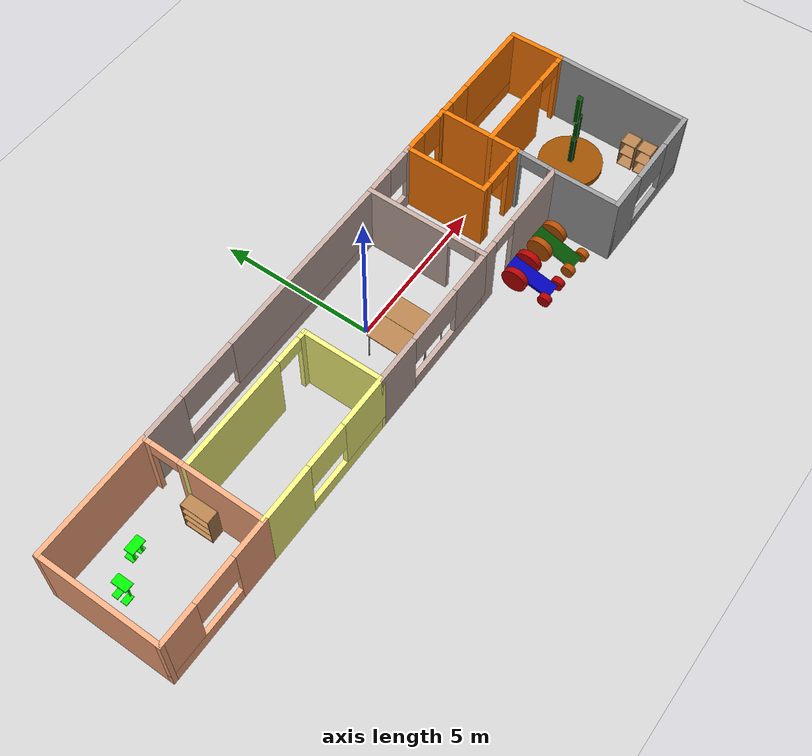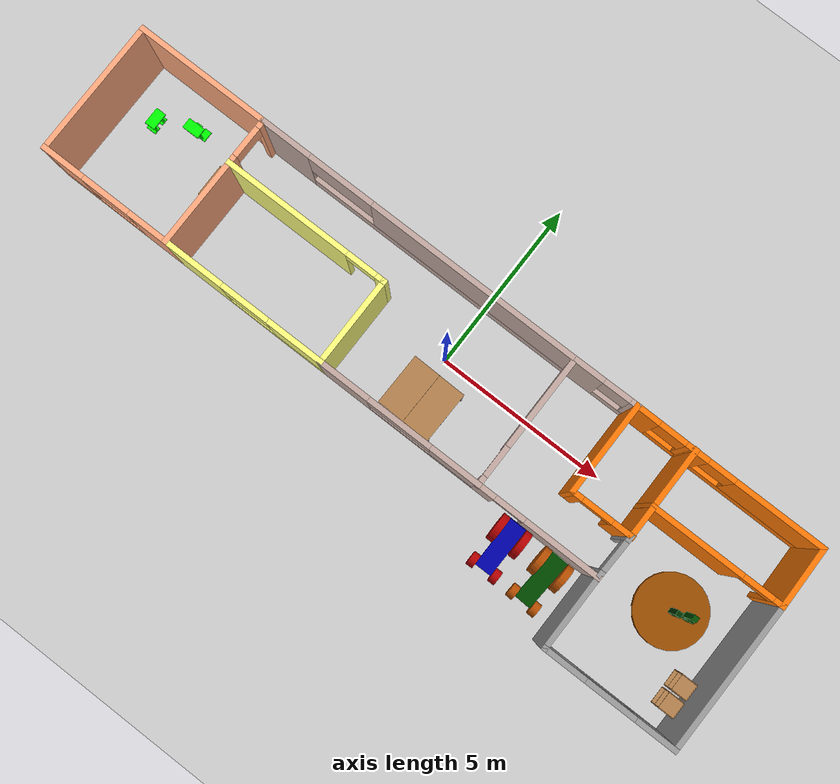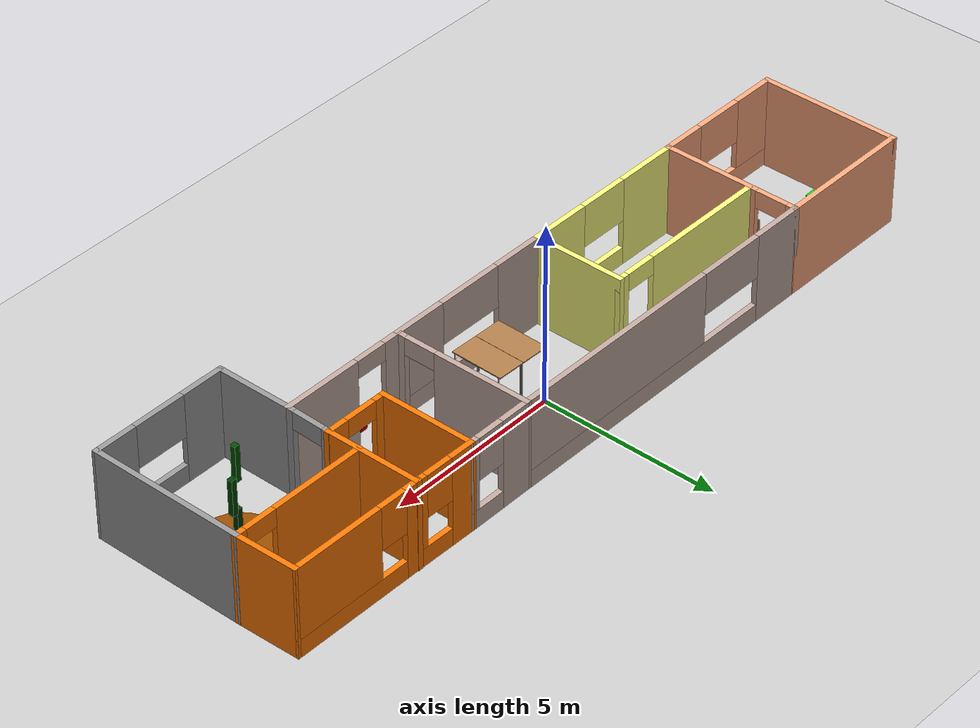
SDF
<sdf version="1.6">
 <world name="default">
  <plugin name="hello" filename="libhello.so"/>
  <light name="sun" type="directional">
   <pose>0 0 10 0 -0 0</pose>
   <diffuse>0.8 0.8 0.8 1</diffuse>
   <specular>0.2 0.2 0.2 1</specular>
   <attenuation>
    <range>1000</range>
    <constant>0.9</constant>
    <linear>0.01</linear>
    <quadratic>0.001</quadratic>
   </attenuation>
   <direction>-0.5 0.1 -0.9</direction>
  </light>
  <model name="ground_plane">
   <static>1</static>
   <link name="link">
    <collision name="collision">
     <geometry><plane><normal>0 0 1</normal><size>100 100</size></plane></geometry>
     <surface><friction><ode><mu>100</mu><mu2>50</mu2></ode></friction></surface>
    </collision>
    <visual name="visual">
     <cast_shadows>0</cast_shadows>
     <geometry><plane><normal>0 0 1</normal><size>100 100</size></plane></geometry>
     <material>
      <script><uri>file://media/materials/scripts/gazebo.material</uri><name>Gazebo/Grey</name></script>
     </material>
    </visual>
   </link>
  </model>
  <gravity>0 0 -9.8</gravity>
  <magnetic_field>6e-06 2.3e-05 -4.2e-05</magnetic_field>
  <atmosphere type="adiabatic"/>
  <physics name="default_physics" default="0" type="ode">
   <max_step_size>0.001</max_step_size>
   <real_time_factor>1</real_time_factor>
   <real_time_update_rate>1000</real_time_update_rate>
  </physics>
  <scene><ambient>0.4 0.4 0.4 1</ambient><background>0.7 0.7 0.7 1</background><shadows>1</shadows></scene>
  <spherical_coordinates>
   <surface_model>EARTH_WGS84</surface_model>
   <latitude_deg>0</latitude_deg>
   <longitude_deg>0</longitude_deg>
   <elevation>0</elevation>
   <heading_deg>0</heading_deg>
  </spherical_coordinates>
  <model name="Building">
   <pose>-0.39074 -1.25242 0 0 -0 0</pose>
   <link name="Wall_0">
    <collision name="Wall_0_Collision">
     <geometry><box><size>4 0.15 2.5</size></box></geometry>
     <pose>0 0 1.25 0 -0 0</pose>
    </collision>
    <visual name="Wall_0_Visual">
     <pose>0 0 1.25 0 -0 0</pose>
     <geometry><box><size>4 0.15 2.5</size></box></geometry>
     <material>
      <script><uri>file://media/materials/scripts/gazebo.material</uri><name>Gazebo/Grey</name></script>
      <ambient>1 0.666667 0.498039 1</ambient>
     </material>
     <meta><layer>0</layer></meta>
    </visual>
    <pose>-8.59174 2.96861 0 0 -0 0</pose>
   </link>
   <link name="Wall_11">
    <collision name="Wall_11_Collision">
     <geometry><box><size>2.65 0.15 2.5</size></box></geometry>
     <pose>0 0 1.25 0 -0 0</pose>
    </collision>
    <visual name="Wall_11_Visual">
     <pose>0 0 1.25 0 -0 0</pose>
     <geometry><box><size>2.65 0.15 2.5</size></box></geometry>
     <material>
      <script><uri>file://media/materials/scripts/gazebo.material</uri><name>Gazebo/Grey</name></script>
      <ambient>1 0.666667 0.498039 1</ambient>
     </material>
     <meta><layer>0</layer></meta>
    </visual>
    <pose>-6.66674 0.368612 0 0 0 -1.5708</pose>
   </link>
   <link name="Wall_13">
    <pose>-4.24174 -0.881388 0 0 -0 0</pose>
    <visual name="Wall_13_Visual_0">
     <pose>-1.57798 0 1.25 0 -0 0</pose>
     <geometry><box><size>1.84404 0.15 2.5</size></box></geometry>
     <material>
      <script><uri>file://media/materials/scripts/gazebo.material</uri><name>Gazebo/Grey</name></script>
      <ambient>1 1 0.498039 1</ambient>
     </material>
     <meta><layer>0</layer></meta>
    </visual>
    <collision name="Wall_13_Collision_0">
     <geometry><box><size>1.84404 0.15 2.5</size></box></geometry>
     <pose>-1.57798 0 1.25 0 -0 0</pose>
    </collision>
    <visual name="Wall_13_Visual_1">
     <pose>0.922019 0 0.25 0 -0 0</pose>
     <geometry><box><size>3.15596 0.15 0.5</size></box></geometry>
     <material>
      <script><uri>file://media/materials/scripts/gazebo.material</uri><name>Gazebo/Grey</name></script>
      <ambient>1 1 0.498039 1</ambient>
     </material>
     <meta><layer>0</layer></meta>
    </visual>
    <collision name="Wall_13_Collision_1">
     <geometry><box><size>3.15596 0.15 0.5</size></box></geometry>
     <pose>0.922019 0 0.25 0 -0 0</pose>
    </collision>
    <visual name="Wall_13_Visual_2">
     <pose>1.64384 0 1.5 0 -0 0</pose>
     <geometry><box><size>1.71233 0.15 2</size></box></geometry>
     <material>
      <script><uri>file://media/materials/scripts/gazebo.material</uri><name>Gazebo/Grey</name></script>
      <ambient>1 1 0.498039 1</ambient>
     </material>
     <meta><layer>0</layer></meta>
    </visual>
    <collision name="Wall_13_Collision_2">
     <geometry><box><size>1.71233 0.15 2</size></box></geometry>
     <pose>1.64384 0 1.5 0 -0 0</pose>
    </collision>
    <visual name="Wall_13_Visual_3">
     <pose>0.065854 0 1.9 0 -0 0</pose>
     <geometry><box><size>1.44363 0.15 1.2</size></box></geometry>
     <material>
      <script><uri>file://media/materials/scripts/gazebo.material</uri><name>Gazebo/Grey</name></script>
      <ambient>1 1 0.498039 1</ambient>
     </material>
     <meta><layer>0</layer></meta>
    </visual>
    <collision name="Wall_13_Collision_3">
     <geometry><box><size>1.44363 0.15 1.2</size></box></geometry>
     <pose>0.065854 0 1.9 0 -0 0</pose>
    </collision>
   </link>
   <link name="Wall_14">
    <collision name="Wall_14_Collision">
     <geometry><box><size>2.65 0.15 2.5</size></box></geometry>
     <pose>0 0 1.25 0 -0 0</pose>
    </collision>
    <visual name="Wall_14_Visual">
     <pose>0 0 1.25 0 -0 0</pose>
     <geometry><box><size>2.65 0.15 2.5</size></box></geometry>
     <material>
      <script><uri>file://media/materials/scripts/gazebo.material</uri><name>Gazebo/Grey</name></script>
      <ambient>1 1 0.498039 1</ambient>
     </material>
     <meta><layer>0</layer></meta>
    </visual>
    <pose>-1.81674 0.368612 0 0 -0 1.5708</pose>
   </link>
   <link name="Wall_16">
    <pose>0.608263 -0.881388 0 0 -0 0</pose>
    <visual name="Wall_16_Visual_0">
     <pose>-1.72009 0 1.25 0 -0 0</pose>
     <geometry><box><size>1.55982 0.15 2.5</size></box></geometry>
     <material>
      <script><uri>file://media/materials/scripts/gazebo.material</uri><name>Gazebo/Grey</name></script>
      <ambient>0.760784 0.662745 0.627451 1</ambient>
     </material>
     <meta><layer>0</layer></meta>
    </visual>
    <collision name="Wall_16_Collision_0">
     <geometry><box><size>1.55982 0.15 2.5</size></box></geometry>
     <pose>-1.72009 0 1.25 0 -0 0</pose>
    </collision>
    <visual name="Wall_16_Visual_1">
     <pose>0.779909 0 0.25 0 -0 0</pose>
     <geometry><box><size>3.44018 0.15 0.5</size></box></geometry>
     <material>
      <script><uri>file://media/materials/scripts/gazebo.material</uri><name>Gazebo/Grey</name></script>
      <ambient>0.760784 0.662745 0.627451 1</ambient>
     </material>
     <meta><layer>0</layer></meta>
    </visual>
    <collision name="Wall_16_Collision_1">
     <geometry><box><size>3.44018 0.15 0.5</size></box></geometry>
     <pose>0.779909 0 0.25 0 -0 0</pose>
    </collision>
    <visual name="Wall_16_Visual_2">
     <pose>1.73303 0 1.5 0 -0 0</pose>
     <geometry><box><size>1.53394 0.15 2</size></box></geometry>
     <material>
      <script><uri>file://media/materials/scripts/gazebo.material</uri><name>Gazebo/Grey</name></script>
      <ambient>0.760784 0.662745 0.627451 1</ambient>
     </material>
     <meta><layer>0</layer></meta>
    </visual>
    <collision name="Wall_16_Collision_2">
     <geometry><box><size>1.53394 0.15 2</size></box></geometry>
     <pose>1.73303 0 1.5 0 -0 0</pose>
    </collision>
    <visual name="Wall_16_Visual_3">
     <pose>0.012941 0 1.9 0 -0 0</pose>
     <geometry><box><size>1.90625 0.15 1.2</size></box></geometry>
     <material>
      <script><uri>file://media/materials/scripts/gazebo.material</uri><name>Gazebo/Grey</name></script>
      <ambient>0.760784 0.662745 0.627451 1</ambient>
     </material>
     <meta><layer>0</layer></meta>
    </visual>
    <collision name="Wall_16_Collision_3">
     <geometry><box><size>1.90625 0.15 1.2</size></box></geometry>
     <pose>0.012941 0 1.9 0 -0 0</pose>
    </collision>
   </link>
   <link name="Wall_18">
    <pose>3.03326 1.04361 0 0 -0 1.5708</pose>
    <visual name="Wall_18_Visual_0">
     <pose>-1.83502 0 1.25 0 -0 0</pose>
     <geometry><box><size>0.329952 0.15 2.5</size></box></geometry>
     <material>
      <script><uri>file://media/materials/scripts/gazebo.material</uri><name>Gazebo/Grey</name></script>
      <ambient>0.760784 0.662745 0.627451 1</ambient>
     </material>
     <meta><layer>0</layer></meta>
    </visual>
    <collision name="Wall_18_Collision_0">
     <geometry><box><size>0.329952 0.15 2.5</size></box></geometry>
     <pose>-1.83502 0 1.25 0 -0 0</pose>
    </collision>
    <visual name="Wall_18_Visual_1">
     <pose>0.614976 0 1.25 0 -0 0</pose>
     <geometry><box><size>2.77005 0.15 2.5</size></box></geometry>
     <material>
      <script><uri>file://media/materials/scripts/gazebo.material</uri><name>Gazebo/Grey</name></script>
      <ambient>0.760784 0.662745 0.627451 1</ambient>
     </material>
     <meta><layer>0</layer></meta>
    </visual>
    <collision name="Wall_18_Collision_1">
     <geometry><box><size>2.77005 0.15 2.5</size></box></geometry>
     <pose>0.614976 0 1.25 0 -0 0</pose>
    </collision>
    <visual name="Wall_18_Visual_2">
     <pose>-1.22005 0 2.25 0 -0 0</pose>
     <geometry><box><size>0.9 0.15 0.5</size></box></geometry>
     <material>
      <script><uri>file://media/materials/scripts/gazebo.material</uri><name>Gazebo/Grey</name></script>
      <ambient>0.760784 0.662745 0.627451 1</ambient>
     </material>
     <meta><layer>0</layer></meta>
    </visual>
    <collision name="Wall_18_Collision_2">
     <geometry><box><size>0.9 0.15 0.5</size></box></geometry>
     <pose>-1.22005 0 2.25 0 -0 0</pose>
    </collision>
   </link>
   <link name="Wall_2">
    <pose>-8.59174 -0.881388 0 0 -0 3.14159</pose>
    <visual name="Wall_2_Visual_0">
     <pose>-1.37646 0 1.25 0 -0 0</pose>
     <geometry><box><size>1.24709 0.15 2.5</size></box></geometry>
     <material>
      <script><uri>file://media/materials/scripts/gazebo.material</uri><name>Gazebo/Grey</name></script>
      <ambient>1 0.666667 0.498039 1</ambient>
     </material>
     <meta><layer>0</layer></meta>
    </visual>
    <collision name="Wall_2_Collision_0">
     <geometry><box><size>1.24709 0.15 2.5</size></box></geometry>
     <pose>-1.37646 0 1.25 0 -0 0</pose>
    </collision>
    <visual name="Wall_2_Visual_1">
     <pose>0.623543 0 0.25 0 -0 0</pose>
     <geometry><box><size>2.75291 0.15 0.5</size></box></geometry>
     <material>
      <script><uri>file://media/materials/scripts/gazebo.material</uri><name>Gazebo/Grey</name></script>
      <ambient>1 0.666667 0.498039 1</ambient>
     </material>
     <meta><layer>0</layer></meta>
    </visual>
    <collision name="Wall_2_Collision_1">
     <geometry><box><size>2.75291 0.15 0.5</size></box></geometry>
     <pose>0.623543 0 0.25 0 -0 0</pose>
    </collision>
    <visual name="Wall_2_Visual_2">
     <pose>1.34536 0 1.5 0 -0 0</pose>
     <geometry><box><size>1.30928 0.15 2</size></box></geometry>
     <material>
      <script><uri>file://media/materials/scripts/gazebo.material</uri><name>Gazebo/Grey</name></script>
      <ambient>1 0.666667 0.498039 1</ambient>
     </material>
     <meta><layer>0</layer></meta>
    </visual>
    <collision name="Wall_2_Collision_2">
     <geometry><box><size>1.30928 0.15 2</size></box></geometry>
     <pose>1.34536 0 1.5 0 -0 0</pose>
    </collision>
    <visual name="Wall_2_Visual_3">
     <pose>-0.031096 0 1.9 0 -0 0</pose>
     <geometry><box><size>1.44363 0.15 1.2</size></box></geometry>
     <material>
      <script><uri>file://media/materials/scripts/gazebo.material</uri><name>Gazebo/Grey</name></script>
      <ambient>1 0.666667 0.498039 1</ambient>
     </material>
     <meta><layer>0</layer></meta>
    </visual>
    <collision name="Wall_2_Collision_3">
     <geometry><box><size>1.44363 0.15 1.2</size></box></geometry>
     <pose>-0.031096 0 1.9 0 -0 0</pose>
    </collision>
   </link>
   <link name="Wall_20">
    <pose>4.83326 -0.881388 0 0 -0 0</pose>
    <visual name="Wall_20_Visual_0">
     <pose>-1.58402 0 1.25 0 -0 0</pose>
     <geometry><box><size>0.581965 0.15 2.5</size></box></geometry>
     <material>
      <script><uri>file://media/materials/scripts/gazebo.material</uri><name>Gazebo/Grey</name></script>
      <ambient>0.760784 0.662745 0.627451 1</ambient>
     </material>
     <meta><layer>0</layer></meta>
    </visual>
    <collision name="Wall_20_Collision_0">
     <geometry><box><size>0.581965 0.15 2.5</size></box></geometry>
     <pose>-1.58402 0 1.25 0 -0 0</pose>
    </collision>
    <visual name="Wall_20_Visual_1">
     <pose>0.740982 0 1.25 0 -0 0</pose>
     <geometry><box><size>2.26803 0.15 2.5</size></box></geometry>
     <material>
      <script><uri>file://media/materials/scripts/gazebo.material</uri><name>Gazebo/Grey</name></script>
      <ambient>0.760784 0.662745 0.627451 1</ambient>
     </material>
     <meta><layer>0</layer></meta>
    </visual>
    <collision name="Wall_20_Collision_1">
     <geometry><box><size>2.26803 0.15 2.5</size></box></geometry>
     <pose>0.740982 0 1.25 0 -0 0</pose>
    </collision>
    <visual name="Wall_20_Visual_2">
     <pose>-0.843035 0 2.25 0 -0 0</pose>
     <geometry><box><size>0.9 0.15 0.5</size></box></geometry>
     <material>
      <script><uri>file://media/materials/scripts/gazebo.material</uri><name>Gazebo/Grey</name></script>
      <ambient>0.760784 0.662745 0.627451 1</ambient>
     </material>
     <meta><layer>0</layer></meta>
    </visual>
    <collision name="Wall_20_Collision_2">
     <geometry><box><size>0.9 0.15 0.5</size></box></geometry>
     <pose>-0.843035 0 2.25 0 -0 0</pose>
    </collision>
   </link>
   <link name="Wall_21">
    <collision name="Wall_21_Collision">
     <geometry><box><size>2.25 0.15 2.5</size></box></geometry>
     <pose>0 0 1.25 0 -0 0</pose>
    </collision>
    <visual name="Wall_21_Visual">
     <pose>0 0 1.25 0 -0 0</pose>
     <geometry><box><size>2.25 0.15 2.5</size></box></geometry>
     <material>
      <script><uri>file://media/materials/scripts/gazebo.material</uri><name>Gazebo/Grey</name></script>
      <ambient>0.52549 0.52549 0.52549 1</ambient>
     </material>
     <meta><layer>0</layer></meta>
    </visual>
    <pose>6.63326 -1.93139 0 0 0 -1.5708</pose>
   </link>
   <link name="Wall_22">
    <pose>8.55826 -2.98139 0 0 -0 0</pose>
    <visual name="Wall_22_Visual_0">
     <pose>-1.35198 0 1.25 0 -0 0</pose>
     <geometry><box><size>1.29604 0.15 2.5</size></box></geometry>
     <material>
      <script><uri>file://media/materials/scripts/gazebo.material</uri><name>Gazebo/Grey</name></script>
      <ambient>0.52549 0.52549 0.52549 1</ambient>
     </material>
     <meta><layer>0</layer></meta>
    </visual>
    <collision name="Wall_22_Collision_0">
     <geometry><box><size>1.29604 0.15 2.5</size></box></geometry>
     <pose>-1.35198 0 1.25 0 -0 0</pose>
    </collision>
    <visual name="Wall_22_Visual_1">
     <pose>0.648021 0 0.25 0 -0 0</pose>
     <geometry><box><size>2.70396 0.15 0.5</size></box></geometry>
     <material>
      <script><uri>file://media/materials/scripts/gazebo.material</uri><name>Gazebo/Grey</name></script>
      <ambient>0.52549 0.52549 0.52549 1</ambient>
     </material>
     <meta><layer>0</layer></meta>
    </visual>
    <collision name="Wall_22_Collision_1">
     <geometry><box><size>2.70396 0.15 0.5</size></box></geometry>
     <pose>0.648021 0 0.25 0 -0 0</pose>
    </collision>
    <visual name="Wall_22_Visual_2">
     <pose>1.38995 0 1.5 0 -0 0</pose>
     <geometry><box><size>1.2201 0.15 2</size></box></geometry>
     <material>
      <script><uri>file://media/materials/scripts/gazebo.material</uri><name>Gazebo/Grey</name></script>
      <ambient>0.52549 0.52549 0.52549 1</ambient>
     </material>
     <meta><layer>0</layer></meta>
    </visual>
    <collision name="Wall_22_Collision_2">
     <geometry><box><size>1.2201 0.15 2</size></box></geometry>
     <pose>1.38995 0 1.5 0 -0 0</pose>
    </collision>
    <visual name="Wall_22_Visual_3">
     <pose>0.037972 0 1.9 0 -0 0</pose>
     <geometry><box><size>1.48386 0.15 1.2</size></box></geometry>
     <material>
      <script><uri>file://media/materials/scripts/gazebo.material</uri><name>Gazebo/Grey</name></script>
      <ambient>0.52549 0.52549 0.52549 1</ambient>
     </material>
     <meta><layer>0</layer></meta>
    </visual>
    <collision name="Wall_22_Collision_3">
     <geometry><box><size>1.48386 0.15 1.2</size></box></geometry>
     <pose>0.037972 0 1.9 0 -0 0</pose>
    </collision>
   </link>
   <link name="Wall_29">
    <collision name="Wall_29_Collision">
     <geometry><box><size>2.75 0.15 2.5</size></box></geometry>
     <pose>0 0 1.25 0 -0 0</pose>
    </collision>
    <visual name="Wall_29_Visual">
     <pose>0 0 1.25 0 -0 0</pose>
     <geometry><box><size>2.75 0.15 2.5</size></box></geometry>
     <material>
      <script><uri>file://media/materials/scripts/gazebo.material</uri><name>Gazebo/Grey</name></script>
      <ambient>0.996078 0.47451 0.0196078 1</ambient>
     </material>
     <meta><layer>0</layer></meta>
    </visual>
    <pose>4.91545 1.68139 0 0 0 -1.5708</pose>
   </link>
   <link name="Wall_3">
    <collision name="Wall_3_Collision">
     <geometry><box><size>4 0.15 2.5</size></box></geometry>
     <pose>0 0 1.25 0 -0 0</pose>
    </collision>
    <visual name="Wall_3_Visual">
     <pose>0 0 1.25 0 -0 0</pose>
     <geometry><box><size>4 0.15 2.5</size></box></geometry>
     <material>
      <script><uri>file://media/materials/scripts/gazebo.material</uri><name>Gazebo/Grey</name></script>
      <ambient>1 0.666667 0.498039 1</ambient>
     </material>
     <meta><layer>0</layer></meta>
    </visual>
    <pose>-10.5167 1.04361 0 0 -0 1.5708</pose>
   </link>
   <link name="Wall_30">
    <pose>5.8029 0.381395 0 0 -0 0</pose>
    <visual name="Wall_30_Visual_0">
     <pose>-0.770642 0 1.25 0 -0 0</pose>
     <geometry><box><size>0.383617 0.15 2.5</size></box></geometry>
     <material>
      <script><uri>file://media/materials/scripts/gazebo.material</uri><name>Gazebo/Grey</name></script>
      <ambient>0.996078 0.47451 0.0196078 1</ambient>
     </material>
     <meta><layer>0</layer></meta>
    </visual>
    <collision name="Wall_30_Collision_0">
     <geometry><box><size>0.383617 0.15 2.5</size></box></geometry>
     <pose>-0.770642 0 1.25 0 -0 0</pose>
    </collision>
    <visual name="Wall_30_Visual_1">
     <pose>0.641808 0 1.25 0 -0 0</pose>
     <geometry><box><size>0.641284 0.15 2.5</size></box></geometry>
     <material>
      <script><uri>file://media/materials/scripts/gazebo.material</uri><name>Gazebo/Grey</name></script>
      <ambient>0.996078 0.47451 0.0196078 1</ambient>
     </material>
     <meta><layer>0</layer></meta>
    </visual>
    <collision name="Wall_30_Collision_1">
     <geometry><box><size>0.641284 0.15 2.5</size></box></geometry>
     <pose>0.641808 0 1.25 0 -0 0</pose>
    </collision>
    <visual name="Wall_30_Visual_2">
     <pose>-0.128834 0 2.25 0 -0 0</pose>
     <geometry><box><size>0.9 0.15 0.5</size></box></geometry>
     <material>
      <script><uri>file://media/materials/scripts/gazebo.material</uri><name>Gazebo/Grey</name></script>
      <ambient>0.996078 0.47451 0.0196078 1</ambient>
     </material>
     <meta><layer>0</layer></meta>
    </visual>
    <collision name="Wall_30_Collision_2">
     <geometry><box><size>0.9 0.15 0.5</size></box></geometry>
     <pose>-0.128834 0 2.25 0 -0 0</pose>
    </collision>
   </link>
   <link name="Wall_32">
    <pose>8.59033 1.27174 0 0 -0 0</pose>
    <visual name="Wall_32_Visual_0">
     <pose>-0.618641 0 1.25 0 -0 0</pose>
     <geometry><box><size>2.76272 0.15 2.5</size></box></geometry>
     <material>
      <script><uri>file://media/materials/scripts/gazebo.material</uri><name>Gazebo/Grey</name></script>
      <ambient>0.996078 0.47451 0.0196078 1</ambient>
     </material>
     <meta><layer>0</layer></meta>
    </visual>
    <collision name="Wall_32_Collision_0">
     <geometry><box><size>2.76272 0.15 2.5</size></box></geometry>
     <pose>-0.618641 0 1.25 0 -0 0</pose>
    </collision>
    <visual name="Wall_32_Visual_1">
     <pose>1.83136 0 1.25 0 -0 0</pose>
     <geometry><box><size>0.337282 0.15 2.5</size></box></geometry>
     <material>
      <script><uri>file://media/materials/scripts/gazebo.material</uri><name>Gazebo/Grey</name></script>
      <ambient>0.996078 0.47451 0.0196078 1</ambient>
     </material>
     <meta><layer>0</layer></meta>
    </visual>
    <collision name="Wall_32_Collision_1">
     <geometry><box><size>0.337282 0.15 2.5</size></box></geometry>
     <pose>1.83136 0 1.25 0 -0 0</pose>
    </collision>
    <visual name="Wall_32_Visual_2">
     <pose>1.21272 0 2.25 0 -0 0</pose>
     <geometry><box><size>0.9 0.15 0.5</size></box></geometry>
     <material>
      <script><uri>file://media/materials/scripts/gazebo.material</uri><name>Gazebo/Grey</name></script>
      <ambient>0.996078 0.47451 0.0196078 1</ambient>
     </material>
     <meta><layer>0</layer></meta>
    </visual>
    <collision name="Wall_32_Collision_2">
     <geometry><box><size>0.9 0.15 0.5</size></box></geometry>
     <pose>1.21272 0 2.25 0 -0 0</pose>
    </collision>
   </link>
   <link name="Wall_34">
    <pose>3.97436 2.975 0 0 -0 0.006791</pose>
    <visual name="Wall_34_Visual_0">
     <pose>-0.53739 0 1.25 0 -0 0</pose>
     <geometry><box><size>0.957452 0.15 2.5</size></box></geometry>
     <material>
      <script><uri>file://media/materials/scripts/gazebo.material</uri><name>Gazebo/Grey</name></script>
      <ambient>0.760784 0.662745 0.627451 1</ambient>
     </material>
     <meta><layer>0</layer></meta>
    </visual>
    <collision name="Wall_34_Collision_0">
     <geometry><box><size>0.957452 0.15 2.5</size></box></geometry>
     <pose>-0.53739 0 1.25 0 -0 0</pose>
    </collision>
    <visual name="Wall_34_Visual_1">
     <pose>0.478726 0 0.25 0 -0 0</pose>
     <geometry><box><size>1.07478 0.15 0.5</size></box></geometry>
     <material>
      <script><uri>file://media/materials/scripts/gazebo.material</uri><name>Gazebo/Grey</name></script>
      <ambient>0.760784 0.662745 0.627451 1</ambient>
     </material>
     <meta><layer>0</layer></meta>
    </visual>
    <collision name="Wall_34_Collision_1">
     <geometry><box><size>1.07478 0.15 0.5</size></box></geometry>
     <pose>0.478726 0 0.25 0 -0 0</pose>
    </collision>
    <visual name="Wall_34_Visual_2">
     <pose>0.878726 0 1.5 0 -0 0</pose>
     <geometry><box><size>0.27478 0.15 2</size></box></geometry>
     <material>
      <script><uri>file://media/materials/scripts/gazebo.material</uri><name>Gazebo/Grey</name></script>
      <ambient>0.760784 0.662745 0.627451 1</ambient>
     </material>
     <meta><layer>0</layer></meta>
    </visual>
    <collision name="Wall_34_Collision_2">
     <geometry><box><size>0.27478 0.15 2</size></box></geometry>
     <pose>0.878726 0 1.5 0 -0 0</pose>
    </collision>
    <visual name="Wall_34_Visual_3">
     <pose>0.341336 0 1.9 0 -0 0</pose>
     <geometry><box><size>0.8 0.15 1.2</size></box></geometry>
     <material>
      <script><uri>file://media/materials/scripts/gazebo.material</uri><name>Gazebo/Grey</name></script>
      <ambient>0.760784 0.662745 0.627451 1</ambient>
     </material>
     <meta><layer>0</layer></meta>
    </visual>
    <collision name="Wall_34_Collision_3">
     <geometry><box><size>0.8 0.15 1.2</size></box></geometry>
     <pose>0.341336 0 1.9 0 -0 0</pose>
    </collision>
   </link>
   <link name="Wall_35">
    <pose>5.77436 2.975 0 0 0 -0.007441</pose>
    <visual name="Wall_35_Visual_0">
     <pose>-0.551182 0 1.25 0 -0 0</pose>
     <geometry><box><size>0.765495 0.15 2.5</size></box></geometry>
     <material>
      <script><uri>file://media/materials/scripts/gazebo.material</uri><name>Gazebo/Grey</name></script>
      <ambient>0.996078 0.47451 0.0196078 1</ambient>
     </material>
     <meta><layer>0</layer></meta>
    </visual>
    <collision name="Wall_35_Collision_0">
     <geometry><box><size>0.765495 0.15 2.5</size></box></geometry>
     <pose>-0.551182 0 1.25 0 -0 0</pose>
    </collision>
    <visual name="Wall_35_Visual_1">
     <pose>0.382747 0 0.25 0 -0 0</pose>
     <geometry><box><size>1.10236 0.15 0.5</size></box></geometry>
     <material>
      <script><uri>file://media/materials/scripts/gazebo.material</uri><name>Gazebo/Grey</name></script>
      <ambient>0.996078 0.47451 0.0196078 1</ambient>
     </material>
     <meta><layer>0</layer></meta>
    </visual>
    <collision name="Wall_35_Collision_1">
     <geometry><box><size>1.10236 0.15 0.5</size></box></geometry>
     <pose>0.382747 0 0.25 0 -0 0</pose>
    </collision>
    <visual name="Wall_35_Visual_2">
     <pose>0.782747 0 1.5 0 -0 0</pose>
     <geometry><box><size>0.302364 0.15 2</size></box></geometry>
     <material>
      <script><uri>file://media/materials/scripts/gazebo.material</uri><name>Gazebo/Grey</name></script>
      <ambient>0.996078 0.47451 0.0196078 1</ambient>
     </material>
     <meta><layer>0</layer></meta>
    </visual>
    <collision name="Wall_35_Collision_2">
     <geometry><box><size>0.302364 0.15 2</size></box></geometry>
     <pose>0.782747 0 1.5 0 -0 0</pose>
    </collision>
    <visual name="Wall_35_Visual_3">
     <pose>0.231565 0 1.9 0 -0 0</pose>
     <geometry><box><size>0.8 0.15 1.2</size></box></geometry>
     <material>
      <script><uri>file://media/materials/scripts/gazebo.material</uri><name>Gazebo/Grey</name></script>
      <ambient>0.996078 0.47451 0.0196078 1</ambient>
     </material>
     <meta><layer>0</layer></meta>
    </visual>
    <collision name="Wall_35_Collision_3">
     <geometry><box><size>0.8 0.15 1.2</size></box></geometry>
     <pose>0.231565 0 1.9 0 -0 0</pose>
    </collision>
   </link>
   <link name="Wall_36">
    <pose>8.55826 2.96861 0 0 -0 0</pose>
    <visual name="Wall_36_Visual_0">
     <pose>-1.74224 0 1.25 0 -0 0</pose>
     <geometry><box><size>0.515525 0.15 2.5</size></box></geometry>
     <material>
      <script><uri>file://media/materials/scripts/gazebo.material</uri><name>Gazebo/Grey</name></script>
      <ambient>0.996078 0.47451 0.0196078 1</ambient>
     </material>
     <meta><layer>0</layer></meta>
    </visual>
    <collision name="Wall_36_Collision_0">
     <geometry><box><size>0.515525 0.15 2.5</size></box></geometry>
     <pose>-1.74224 0 1.25 0 -0 0</pose>
    </collision>
    <visual name="Wall_36_Visual_1">
     <pose>0.257763 0 0.25 0 -0 0</pose>
     <geometry><box><size>3.48448 0.15 0.5</size></box></geometry>
     <material>
      <script><uri>file://media/materials/scripts/gazebo.material</uri><name>Gazebo/Grey</name></script>
      <ambient>0.996078 0.47451 0.0196078 1</ambient>
     </material>
     <meta><layer>0</layer></meta>
    </visual>
    <collision name="Wall_36_Collision_1">
     <geometry><box><size>3.48448 0.15 0.5</size></box></geometry>
     <pose>0.257763 0 0.25 0 -0 0</pose>
    </collision>
    <visual name="Wall_36_Visual_2">
     <pose>0.657763 0 1.5 0 -0 0</pose>
     <geometry><box><size>2.68447 0.15 2</size></box></geometry>
     <material>
      <script><uri>file://media/materials/scripts/gazebo.material</uri><name>Gazebo/Grey</name></script>
      <ambient>0.996078 0.47451 0.0196078 1</ambient>
     </material>
     <meta><layer>0</layer></meta>
    </visual>
    <collision name="Wall_36_Collision_2">
     <geometry><box><size>2.68447 0.15 2</size></box></geometry>
     <pose>0.657763 0 1.5 0 -0 0</pose>
    </collision>
    <visual name="Wall_36_Visual_3">
     <pose>-1.08448 0 1.9 0 -0 0</pose>
     <geometry><box><size>0.8 0.15 1.2</size></box></geometry>
     <material>
      <script><uri>file://media/materials/scripts/gazebo.material</uri><name>Gazebo/Grey</name></script>
      <ambient>0.996078 0.47451 0.0196078 1</ambient>
     </material>
     <meta><layer>0</layer></meta>
    </visual>
    <collision name="Wall_36_Collision_3">
     <geometry><box><size>0.8 0.15 1.2</size></box></geometry>
     <pose>-1.08448 0 1.9 0 -0 0</pose>
    </collision>
   </link>
   <link name="Wall_38">
    <collision name="Wall_38_Collision">
     <geometry><box><size>2.75 0.15 2.5</size></box></geometry>
     <pose>0 0 1.25 0 -0 0</pose>
    </collision>
    <visual name="Wall_38_Visual">
     <pose>0 0 1.25 0 -0 0</pose>
     <geometry><box><size>2.75 0.15 2.5</size></box></geometry>
     <material>
      <script><uri>file://media/materials/scripts/gazebo.material</uri><name>Gazebo/Grey</name></script>
      <ambient>0.996078 0.47451 0.0196078 1</ambient>
     </material>
     <meta><layer>0</layer></meta>
    </visual>
    <pose>6.67286 1.68139 0 0 -0 1.5708</pose>
   </link>
   <link name="Wall_40">
    <collision name="Wall_40_Collision">
     <geometry><box><size>1.84717 0.15 2.5</size></box></geometry>
     <pose>0 0 1.25 0 -0 0</pose>
    </collision>
    <visual name="Wall_40_Visual">
     <pose>0 0 1.25 0 -0 0</pose>
     <geometry><box><size>1.84717 0.15 2.5</size></box></geometry>
     <material>
      <script><uri>file://media/materials/scripts/gazebo.material</uri><name>Gazebo/Grey</name></script>
      <ambient>0.996078 0.47451 0.0196078 1</ambient>
     </material>
     <meta><layer>0</layer></meta>
    </visual>
    <pose>10.4993 2.12018 0 0 -0 1.58969</pose>
   </link>
   <link name="Wall_42">
    <collision name="Wall_42_Collision">
     <geometry><box><size>4.40325 0.15 2.5</size></box></geometry>
     <pose>0 0 1.25 0 -0 0</pose>
    </collision>
    <visual name="Wall_42_Visual">
     <pose>0 0 1.25 0 -0 0</pose>
     <geometry><box><size>4.40325 0.15 2.5</size></box></geometry>
     <material>
      <script><uri>file://media/materials/scripts/gazebo.material</uri><name>Gazebo/Grey</name></script>
      <ambient>0.52549 0.52549 0.52549 1</ambient>
     </material>
     <meta><layer>0</layer></meta>
    </visual>
    <pose>10.4993 -0.854823 0 0 -0 1.56326</pose>
   </link>
   <link name="Wall_45">
    <pose>6.65306 -0.249996 0 0 -0 1.53945</pose>
    <visual name="Wall_45_Visual_0">
     <pose>-0.573288 0 1.25 0 -0 0</pose>
     <geometry><box><size>0.266828 0.15 2.5</size></box></geometry>
     <material>
      <script><uri>file://media/materials/scripts/gazebo.material</uri><name>Gazebo/Grey</name></script>
      <ambient>0.541176 0.541176 0.541176 1</ambient>
     </material>
     <meta><layer>0</layer></meta>
    </visual>
    <collision name="Wall_45_Collision_0">
     <geometry><box><size>0.266828 0.15 2.5</size></box></geometry>
     <pose>-0.573288 0 1.25 0 -0 0</pose>
    </collision>
    <visual name="Wall_45_Visual_1">
     <pose>0.583414 0 1.25 0 -0 0</pose>
     <geometry><box><size>0.246576 0.15 2.5</size></box></geometry>
     <material>
      <script><uri>file://media/materials/scripts/gazebo.material</uri><name>Gazebo/Grey</name></script>
      <ambient>0.541176 0.541176 0.541176 1</ambient>
     </material>
     <meta><layer>0</layer></meta>
    </visual>
    <collision name="Wall_45_Collision_1">
     <geometry><box><size>0.246576 0.15 2.5</size></box></geometry>
     <pose>0.583414 0 1.25 0 -0 0</pose>
    </collision>
    <visual name="Wall_45_Visual_2">
     <pose>0.010126 0 2.25 0 -0 0</pose>
     <geometry><box><size>0.9 0.15 0.5</size></box></geometry>
     <material>
      <script><uri>file://media/materials/scripts/gazebo.material</uri><name>Gazebo/Grey</name></script>
      <ambient>0.541176 0.541176 0.541176 1</ambient>
     </material>
     <meta><layer>0</layer></meta>
    </visual>
    <collision name="Wall_45_Collision_2">
     <geometry><box><size>0.9 0.15 0.5</size></box></geometry>
     <pose>0.010126 0 2.25 0 -0 0</pose>
    </collision>
   </link>
   <link name="Wall_5">
    <pose>-1.86674 2.96861 0 0 -0 0</pose>
    <visual name="Wall_5_Visual_0">
     <pose>-4.10383 0 1.25 0 -0 0</pose>
     <geometry><box><size>1.54233 0.15 2.5</size></box></geometry>
     <material>
      <script><uri>file://media/materials/scripts/gazebo.material</uri><name>Gazebo/Grey</name></script>
      <ambient>0.760784 0.662745 0.627451 1</ambient>
     </material>
     <meta><layer>0</layer></meta>
    </visual>
    <collision name="Wall_5_Collision_0">
     <geometry><box><size>1.54233 0.15 2.5</size></box></geometry>
     <pose>-4.10383 0 1.25 0 -0 0</pose>
    </collision>
    <visual name="Wall_5_Visual_1">
     <pose>0.771167 0 0.25 0 -0 0</pose>
     <geometry><box><size>8.20767 0.15 0.5</size></box></geometry>
     <material>
      <script><uri>file://media/materials/scripts/gazebo.material</uri><name>Gazebo/Grey</name></script>
      <ambient>0.760784 0.662745 0.627451 1</ambient>
     </material>
     <meta><layer>0</layer></meta>
    </visual>
    <collision name="Wall_5_Collision_1">
     <geometry><box><size>8.20767 0.15 0.5</size></box></geometry>
     <pose>0.771167 0 0.25 0 -0 0</pose>
    </collision>
    <visual name="Wall_5_Visual_2">
     <pose>1.75446 0 1.5 0 -0 0</pose>
     <geometry><box><size>6.24108 0.15 2</size></box></geometry>
     <material>
      <script><uri>file://media/materials/scripts/gazebo.material</uri><name>Gazebo/Grey</name></script>
      <ambient>0.760784 0.662745 0.627451 1</ambient>
     </material>
     <meta><layer>0</layer></meta>
    </visual>
    <collision name="Wall_5_Collision_2">
     <geometry><box><size>6.24108 0.15 2</size></box></geometry>
     <pose>1.75446 0 1.5 0 -0 0</pose>
    </collision>
    <visual name="Wall_5_Visual_3">
     <pose>-2.34937 0 1.9 0 -0 0</pose>
     <geometry><box><size>1.96659 0.15 1.2</size></box></geometry>
     <material>
      <script><uri>file://media/materials/scripts/gazebo.material</uri><name>Gazebo/Grey</name></script>
      <ambient>0.760784 0.662745 0.627451 1</ambient>
     </material>
     <meta><layer>0</layer></meta>
    </visual>
    <collision name="Wall_5_Collision_3">
     <geometry><box><size>1.96659 0.15 1.2</size></box></geometry>
     <pose>-2.34937 0 1.9 0 -0 0</pose>
    </collision>
   </link>
   <link name="Wall_7">
    <pose>-4.24174 1.61861 0 0 -0 3.14159</pose>
    <visual name="Wall_7_Visual_0">
     <pose>-2.3401 0 1.25 0 -0 0</pose>
     <geometry><box><size>0.319798 0.15 2.5</size></box></geometry>
     <material>
      <script><uri>file://media/materials/scripts/gazebo.material</uri><name>Gazebo/Grey</name></script>
      <ambient>1 1 0.498039 1</ambient>
     </material>
     <meta><layer>0</layer></meta>
    </visual>
    <collision name="Wall_7_Collision_0">
     <geometry><box><size>0.319798 0.15 2.5</size></box></geometry>
     <pose>-2.3401 0 1.25 0 -0 0</pose>
    </collision>
    <visual name="Wall_7_Visual_1">
     <pose>0.609899 0 1.25 0 -0 0</pose>
     <geometry><box><size>3.7802 0.15 2.5</size></box></geometry>
     <material>
      <script><uri>file://media/materials/scripts/gazebo.material</uri><name>Gazebo/Grey</name></script>
      <ambient>1 1 0.498039 1</ambient>
     </material>
     <meta><layer>0</layer></meta>
    </visual>
    <collision name="Wall_7_Collision_1">
     <geometry><box><size>3.7802 0.15 2.5</size></box></geometry>
     <pose>0.609899 0 1.25 0 -0 0</pose>
    </collision>
    <visual name="Wall_7_Visual_2">
     <pose>-1.7302 0 2.25 0 -0 0</pose>
     <geometry><box><size>0.9 0.15 0.5</size></box></geometry>
     <material>
      <script><uri>file://media/materials/scripts/gazebo.material</uri><name>Gazebo/Grey</name></script>
      <ambient>1 1 0.498039 1</ambient>
     </material>
     <meta><layer>0</layer></meta>
    </visual>
    <collision name="Wall_7_Collision_2">
     <geometry><box><size>0.9 0.15 0.5</size></box></geometry>
     <pose>-1.7302 0 2.25 0 -0 0</pose>
    </collision>
   </link>
   <link name="Wall_9">
    <pose>-6.66674 2.29361 0 0 -0 1.5708</pose>
    <visual name="Wall_9_Visual_0">
     <pose>-0.604431 0 1.25 0 -0 0</pose>
     <geometry><box><size>0.291139 0.15 2.5</size></box></geometry>
     <material>
      <script><uri>file://media/materials/scripts/gazebo.material</uri><name>Gazebo/Grey</name></script>
      <ambient>1 0.666667 0.498039 1</ambient>
     </material>
     <meta><layer>0</layer></meta>
    </visual>
    <collision name="Wall_9_Collision_0">
     <geometry><box><size>0.291139 0.15 2.5</size></box></geometry>
     <pose>-0.604431 0 1.25 0 -0 0</pose>
    </collision>
    <visual name="Wall_9_Visual_1">
     <pose>0.595569 0 1.25 0 -0 0</pose>
     <geometry><box><size>0.308861 0.15 2.5</size></box></geometry>
     <material>
      <script><uri>file://media/materials/scripts/gazebo.material</uri><name>Gazebo/Grey</name></script>
      <ambient>1 0.666667 0.498039 1</ambient>
     </material>
     <meta><layer>0</layer></meta>
    </visual>
    <collision name="Wall_9_Collision_1">
     <geometry><box><size>0.308861 0.15 2.5</size></box></geometry>
     <pose>0.595569 0 1.25 0 -0 0</pose>
    </collision>
    <visual name="Wall_9_Visual_2">
     <pose>-0.008861 0 2.25 0 -0 0</pose>
     <geometry><box><size>0.9 0.15 0.5</size></box></geometry>
     <material>
      <script><uri>file://media/materials/scripts/gazebo.material</uri><name>Gazebo/Grey</name></script>
      <ambient>1 0.666667 0.498039 1</ambient>
     </material>
     <meta><layer>0</layer></meta>
    </visual>
    <collision name="Wall_9_Collision_2">
     <geometry><box><size>0.9 0.15 0.5</size></box></geometry>
     <pose>-0.008861 0 2.25 0 -0 0</pose>
    </collision>
   </link>
   <static>1</static>
  </model>
  <model name="HumanoidRobot">
   <link name="link_0">
    <pose>0.08559 0.15 -0.26 0 -0 0</pose>
    <inertial>
     <mass>1</mass>
     <inertia>
      <ixx>0.166667</ixx>
      <ixy>0</ixy>
      <ixz>0</ixz>
      <iyy>0.166667</iyy>
      <iyz>0</iyz>
      <izz>0.166667</izz>
     </inertia>
    </inertial>
    <visual name="visual">
     <geometry><box><size>0.3 0.2 0.04</size></box></geometry>
     <material>
      <lighting>1</lighting>
      <script><uri>file://media/materials/scripts/gazebo.material</uri><name>Gazebo/Grey</name></script>
      <shader type="pixel"><normal_map>__default__</normal_map></shader>
      <ambient>0 1 0 1</ambient>
      <diffuse>0 1 0 1</diffuse>
      <specular>0 1 0 1</specular>
      <emissive>0 0 0 1</emissive>
     </material>
    </visual>
    <collision name="collision">
     <geometry><box><size>0.3 0.2 0.04</size></box></geometry>
     <surface>
      <friction>
       <ode><mu>1</mu><mu2>1</mu2><fdir1>0 0 0</fdir1><slip1>0</slip1><slip2>0</slip2></ode>
       <torsional>
        <coefficient>1</coefficient>
        <patch_radius>0</patch_radius>
        <surface_radius>0</surface_radius>
        <use_patch_radius>1</use_patch_radius>
        <ode><slip>0</slip></ode>
       </torsional>
      </friction>
      <bounce><restitution_coefficient>0</restitution_coefficient><threshold>1e+06</threshold></bounce>
      <contact>
       <collide_without_contact>0</collide_without_contact>
       <collide_without_contact_bitmask>1</collide_without_contact_bitmask>
       <collide_bitmask>1</collide_bitmask>
       <ode>
        <soft_cfm>0</soft_cfm>
        <soft_erp>0.2</soft_erp>
        <kp>1e+13</kp>
        <kd>1</kd>
        <max_vel>0.01</max_vel>
        <min_depth>0</min_depth>
       </ode>
       <bullet>
        <split_impulse>1</split_impulse>
        <split_impulse_penetration_threshold>-0.01</split_impulse_penetration_threshold>
        <soft_cfm>0</soft_cfm>
        <soft_erp>0.2</soft_erp>
        <kp>1e+13</kp>
        <kd>1</kd>
       </bullet>
      </contact>
     </surface>
    </collision>
   </link>
   <link name="link_0_clone">
    <pose>0.08646 -0.15 -0.26 0 -0 0</pose>
    <inertial>
     <mass>1</mass>
     <inertia>
      <ixx>0.166667</ixx>
      <ixy>0</ixy>
      <ixz>0</ixz>
      <iyy>0.166667</iyy>
      <iyz>0</iyz>
      <izz>0.166667</izz>
     </inertia>
    </inertial>
    <visual name="visual">
     <geometry><box><size>0.3 0.2 0.04</size></box></geometry>
     <material>
      <lighting>1</lighting>
      <script><uri>file://media/materials/scripts/gazebo.material</uri><name>Gazebo/Grey</name></script>
      <shader type="pixel"><normal_map>__default__</normal_map></shader>
      <ambient>0 1 0 1</ambient>
      <diffuse>0 1 0 1</diffuse>
      <specular>0 1 0 1</specular>
      <emissive>0 0 0 1</emissive>
     </material>
    </visual>
    <collision name="collision">
     <geometry><box><size>0.3 0.2 0.04</size></box></geometry>
     <surface>
      <friction>
       <ode><mu>1</mu><mu2>1</mu2><fdir1>0 0 0</fdir1><slip1>0</slip1><slip2>0</slip2></ode>
       <torsional>
        <coefficient>1</coefficient>
        <patch_radius>0</patch_radius>
        <surface_radius>0</surface_radius>
        <use_patch_radius>1</use_patch_radius>
        <ode><slip>0</slip></ode>
       </torsional>
      </friction>
      <bounce><restitution_coefficient>0</restitution_coefficient><threshold>1e+06</threshold></bounce>
      <contact>
       <collide_without_contact>0</collide_without_contact>
       <collide_without_contact_bitmask>1</collide_without_contact_bitmask>
       <collide_bitmask>1</collide_bitmask>
       <ode>
        <soft_cfm>0</soft_cfm>
        <soft_erp>0.2</soft_erp>
        <kp>1e+13</kp>
        <kd>1</kd>
        <max_vel>0.01</max_vel>
        <min_depth>0</min_depth>
       </ode>
       <bullet>
        <split_impulse>1</split_impulse>
        <split_impulse_penetration_threshold>-0.01</split_impulse_penetration_threshold>
        <soft_cfm>0</soft_cfm>
        <soft_erp>0.2</soft_erp>
        <kp>1e+13</kp>
        <kd>1</kd>
       </bullet>
      </contact>
     </surface>
    </collision>
   </link>
   <link name="link_1">
    <pose>-0.03441 0.15 -0.11 0 -0 0</pose>
    <inertial>
     <mass>1</mass>
     <inertia><ixx>0.145833</ixx><ixy>0</ixy><ixz>0</ixz><iyy>0.145833</iyy><iyz>0</iyz><izz>0.125</izz></inertia>
    </inertial>
    <visual name="visual">
     <geometry><cylinder><radius>0.03</radius><length>0.3</length></cylinder></geometry>
     <material>
      <lighting>1</lighting>
      <script><uri>file://media/materials/scripts/gazebo.material</uri><name>Gazebo/Grey</name></script>
      <shader type="pixel"><normal_map>__default__</normal_map></shader>
      <ambient>0 0.8 0 1</ambient>
      <diffuse>0 0.8 0 1</diffuse>
      <specular>0 0.8 0 1</specular>
      <emissive>0 0 0 1</emissive>
     </material>
    </visual>
    <collision name="collision">
     <geometry><cylinder><radius>0.03</radius><length>0.3</length></cylinder></geometry>
     <surface>
      <friction>
       <ode><mu>1</mu><mu2>1</mu2><fdir1>0 0 0</fdir1><slip1>0</slip1><slip2>0</slip2></ode>
       <torsional>
        <coefficient>1</coefficient>
        <patch_radius>0</patch_radius>
        <surface_radius>0</surface_radius>
        <use_patch_radius>1</use_patch_radius>
        <ode><slip>0</slip></ode>
       </torsional>
      </friction>
      <bounce><restitution_coefficient>0</restitution_coefficient><threshold>1e+06</threshold></bounce>
      <contact>
       <collide_without_contact>0</collide_without_contact>
       <collide_without_contact_bitmask>1</collide_without_contact_bitmask>
       <collide_bitmask>1</collide_bitmask>
       <ode>
        <soft_cfm>0</soft_cfm>
        <soft_erp>0.2</soft_erp>
        <kp>1e+13</kp>
        <kd>1</kd>
        <max_vel>0.01</max_vel>
        <min_depth>0</min_depth>
       </ode>
       <bullet>
        <split_impulse>1</split_impulse>
        <split_impulse_penetration_threshold>-0.01</split_impulse_penetration_threshold>
        <soft_cfm>0</soft_cfm>
        <soft_erp>0.2</soft_erp>
        <kp>1e+13</kp>
        <kd>1</kd>
       </bullet>
      </contact>
     </surface>
    </collision>
   </link>
   <link name="link_1_clone">
    <pose>-0.03441 -0.15 -0.11 0 -0 0</pose>
    <inertial>
     <mass>1</mass>
     <inertia><ixx>0.145833</ixx><ixy>0</ixy><ixz>0</ixz><iyy>0.145833</iyy><iyz>0</iyz><izz>0.125</izz></inertia>
    </inertial>
    <visual name="visual">
     <geometry><cylinder><radius>0.03</radius><length>0.3</length></cylinder></geometry>
     <material>
      <lighting>1</lighting>
      <script><uri>file://media/materials/scripts/gazebo.material</uri><name>Gazebo/Grey</name></script>
      <shader type="pixel"><normal_map>__default__</normal_map></shader>
      <ambient>0 0.8 0 1</ambient>
      <diffuse>0 0.8 0 1</diffuse>
      <specular>0 0.8 0 1</specular>
      <emissive>0 0 0 1</emissive>
     </material>
    </visual>
    <collision name="collision">
     <geometry><cylinder><radius>0.03</radius><length>0.3</length></cylinder></geometry>
     <surface>
      <friction>
       <ode><mu>1</mu><mu2>1</mu2><fdir1>0 0 0</fdir1><slip1>0</slip1><slip2>0</slip2></ode>
       <torsional>
        <coefficient>1</coefficient>
        <patch_radius>0</patch_radius>
        <surface_radius>0</surface_radius>
        <use_patch_radius>1</use_patch_radius>
        <ode><slip>0</slip></ode>
       </torsional>
      </friction>
      <bounce><restitution_coefficient>0</restitution_coefficient><threshold>1e+06</threshold></bounce>
      <contact>
       <collide_without_contact>0</collide_without_contact>
       <collide_without_contact_bitmask>1</collide_without_contact_bitmask>
       <collide_bitmask>1</collide_bitmask>
       <ode>
        <soft_cfm>0</soft_cfm>
        <soft_erp>0.2</soft_erp>
        <kp>1e+13</kp>
        <kd>1</kd>
        <max_vel>0.01</max_vel>
        <min_depth>0</min_depth>
       </ode>
       <bullet>
        <split_impulse>1</split_impulse>
        <split_impulse_penetration_threshold>-0.01</split_impulse_penetration_threshold>
        <soft_cfm>0</soft_cfm>
        <soft_erp>0.2</soft_erp>
        <kp>1e+13</kp>
        <kd>1</kd>
       </bullet>
      </contact>
     </surface>
    </collision>
   </link>
   <link name="link_1_clone_clone">
    <pose>-0.03441 -0.15 0.19 0 -0 0</pose>
    <inertial>
     <mass>1</mass>
     <inertia><ixx>0.145833</ixx><ixy>0</ixy><ixz>0</ixz><iyy>0.145833</iyy><iyz>0</iyz><izz>0.125</izz></inertia>
    </inertial>
    <visual name="visual">
     <geometry><cylinder><radius>0.03</radius><length>0.3</length></cylinder></geometry>
     <material>
      <lighting>1</lighting>
      <script><uri>file://media/materials/scripts/gazebo.material</uri><name>Gazebo/Grey</name></script>
      <shader type="pixel"><normal_map>__default__</normal_map></shader>
      <ambient>0 0.6 0 1</ambient>
      <diffuse>0 0.6 0 1</diffuse>
      <specular>0 0.6 0 1</specular>
      <emissive>0 0 0 1</emissive>
     </material>
    </visual>
    <collision name="collision">
     <geometry><cylinder><radius>0.03</radius><length>0.3</length></cylinder></geometry>
     <surface>
      <friction>
       <ode><mu>1</mu><mu2>1</mu2><fdir1>0 0 0</fdir1><slip1>0</slip1><slip2>0</slip2></ode>
       <torsional>
        <coefficient>1</coefficient>
        <patch_radius>0</patch_radius>
        <surface_radius>0</surface_radius>
        <use_patch_radius>1</use_patch_radius>
        <ode><slip>0</slip></ode>
       </torsional>
      </friction>
      <bounce><restitution_coefficient>0</restitution_coefficient><threshold>1e+06</threshold></bounce>
      <contact>
       <collide_without_contact>0</collide_without_contact>
       <collide_without_contact_bitmask>1</collide_without_contact_bitmask>
       <collide_bitmask>1</collide_bitmask>
       <ode>
        <soft_cfm>0</soft_cfm>
        <soft_erp>0.2</soft_erp>
        <kp>1e+13</kp>
        <kd>1</kd>
        <max_vel>0.01</max_vel>
        <min_depth>0</min_depth>
       </ode>
       <bullet>
        <split_impulse>1</split_impulse>
        <split_impulse_penetration_threshold>-0.01</split_impulse_penetration_threshold>
        <soft_cfm>0</soft_cfm>
        <soft_erp>0.2</soft_erp>
        <kp>1e+13</kp>
        <kd>1</kd>
       </bullet>
      </contact>
     </surface>
    </collision>
   </link>
   <link name="link_1_clone_clone_clone">
    <pose>-0.03441 0.15 0.19 0 -0 0</pose>
    <inertial>
     <mass>1</mass>
     <inertia><ixx>0.145833</ixx><ixy>0</ixy><ixz>0</ixz><iyy>0.145833</iyy><iyz>0</iyz><izz>0.125</izz></inertia>
    </inertial>
    <visual name="visual">
     <geometry><cylinder><radius>0.03</radius><length>0.3</length></cylinder></geometry>
     <material>
      <lighting>1</lighting>
      <script><uri>file://media/materials/scripts/gazebo.material</uri><name>Gazebo/Grey</name></script>
      <shader type="pixel"><normal_map>__default__</normal_map></shader>
      <ambient>0 0.6 0 1</ambient>
      <diffuse>0 0.6 0 1</diffuse>
      <specular>0 0.6 0 1</specular>
      <emissive>0 0 0 1</emissive>
     </material>
    </visual>
    <collision name="collision">
     <geometry><cylinder><radius>0.03</radius><length>0.3</length></cylinder></geometry>
     <surface>
      <friction>
       <ode><mu>1</mu><mu2>1</mu2><fdir1>0 0 0</fdir1><slip1>0</slip1><slip2>0</slip2></ode>
       <torsional>
        <coefficient>1</coefficient>
        <patch_radius>0</patch_radius>
        <surface_radius>0</surface_radius>
        <use_patch_radius>1</use_patch_radius>
        <ode><slip>0</slip></ode>
       </torsional>
      </friction>
      <bounce><restitution_coefficient>0</restitution_coefficient><threshold>1e+06</threshold></bounce>
      <contact>
       <collide_without_contact>0</collide_without_contact>
       <collide_without_contact_bitmask>1</collide_without_contact_bitmask>
       <collide_bitmask>1</collide_bitmask>
       <ode>
        <soft_cfm>0</soft_cfm>
        <soft_erp>0.2</soft_erp>
        <kp>1e+13</kp>
        <kd>1</kd>
        <max_vel>0.01</max_vel>
        <min_depth>0</min_depth>
       </ode>
       <bullet>
        <split_impulse>1</split_impulse>
        <split_impulse_penetration_threshold>-0.01</split_impulse_penetration_threshold>
        <soft_cfm>0</soft_cfm>
        <soft_erp>0.2</soft_erp>
        <kp>1e+13</kp>
        <kd>1</kd>
       </bullet>
      </contact>
     </surface>
    </collision>
   </link>
   <link name="link_2">
    <pose>-0.03441 0 0.36 0 -0 0</pose>
    <inertial>
     <mass>0.0372499</mass>
     <inertia>
      <ixx>0.00120118</ixx>
      <ixy>0</ixy>
      <ixz>0</ixz>
      <iyy>0.00059503</iyy>
      <iyz>0</iyz>
      <izz>0.00165655</izz>
     </inertia>
    </inertial>
    <visual name="visual">
     <geometry><box><size>0.3 0.5 0.05</size></box></geometry>
     <material>
      <lighting>1</lighting>
      <script><uri>file://media/materials/scripts/gazebo.material</uri><name>Gazebo/Grey</name></script>
      <shader type="pixel"><normal_map>__default__</normal_map></shader>
      <ambient>0 1 0 1</ambient>
      <diffuse>0 1 0 1</diffuse>
      <specular>0 1 0 1</specular>
      <emissive>0 0.2 0 1</emissive>
     </material>
    </visual>
    <collision name="collision">
     <geometry><box><size>0.3 0.5 0.05</size></box></geometry>
     <surface>
      <friction>
       <ode><mu>1</mu><mu2>1</mu2><fdir1>0 0 0</fdir1><slip1>0</slip1><slip2>0</slip2></ode>
       <torsional>
        <coefficient>1</coefficient>
        <patch_radius>0</patch_radius>
        <surface_radius>0</surface_radius>
        <use_patch_radius>1</use_patch_radius>
        <ode><slip>0</slip></ode>
       </torsional>
      </friction>
      <bounce><restitution_coefficient>0</restitution_coefficient><threshold>1e+06</threshold></bounce>
      <contact>
       <collide_without_contact>0</collide_without_contact>
       <collide_without_contact_bitmask>1</collide_without_contact_bitmask>
       <collide_bitmask>1</collide_bitmask>
       <ode>
        <soft_cfm>0</soft_cfm>
        <soft_erp>0.2</soft_erp>
        <kp>1e+13</kp>
        <kd>1</kd>
        <max_vel>0.01</max_vel>
        <min_depth>0</min_depth>
       </ode>
       <bullet>
        <split_impulse>1</split_impulse>
        <split_impulse_penetration_threshold>-0.01</split_impulse_penetration_threshold>
        <soft_cfm>0</soft_cfm>
        <soft_erp>0.2</soft_erp>
        <kp>1e+13</kp>
        <kd>1</kd>
       </bullet>
      </contact>
     </surface>
    </collision>
   </link>
   <joint name="link_1_JOINT_0" type="fixed">
    <parent>link_1</parent>
    <child>link_0</child>
    <pose>-0.12 0 0 0 -0 0</pose>
    <physics>
     <ode><limit><cfm>0</cfm><erp>0.2</erp></limit><suspension><cfm>0</cfm><erp>0.2</erp></suspension></ode>
    </physics>
   </joint>
   <joint name="link_1_clone_JOINT_1" type="revolute">
    <parent>link_1_clone</parent>
    <child>link_0_clone</child>
    <pose>-0.12 0 0 0 -0 0</pose>
    <axis>
     <xyz>1 0 0</xyz>
     <use_parent_model_frame>0</use_parent_model_frame>
     <limit>
      <lower>-1.79769e+308</lower>
      <upper>1.79769e+308</upper>
      <effort>-1</effort>
      <velocity>-1</velocity>
     </limit>
     <dynamics>
      <spring_reference>0</spring_reference>
      <spring_stiffness>0</spring_stiffness>
      <damping>0</damping>
     </dynamics>
    </axis>
    <physics>
     <ode><limit><cfm>0</cfm><erp>0.2</erp></limit><suspension><cfm>0</cfm><erp>0.2</erp></suspension></ode>
    </physics>
   </joint>
   <joint name="link_1_clone_clone_JOINT_3" type="revolute">
    <parent>link_1_clone_clone</parent>
    <child>link_1_clone</child>
    <pose>0 0 0.15 0 -0 0</pose>
    <axis>
     <xyz>0 1 0</xyz>
     <use_parent_model_frame>0</use_parent_model_frame>
     <limit>
      <lower>-1.79769e+308</lower>
      <upper>1.79769e+308</upper>
      <effort>-1</effort>
      <velocity>-1</velocity>
     </limit>
     <dynamics>
      <spring_reference>0</spring_reference>
      <spring_stiffness>0</spring_stiffness>
      <damping>0</damping>
     </dynamics>
    </axis>
    <physics>
     <ode><limit><cfm>0</cfm><erp>0.2</erp></limit><suspension><cfm>0</cfm><erp>0.2</erp></suspension></ode>
    </physics>
   </joint>
   <joint name="link_1_clone_clone_clone_JOINT_4" type="revolute">
    <parent>link_1_clone_clone_clone</parent>
    <child>link_1</child>
    <pose>0 0 0.15 0 -0 0</pose>
    <axis>
     <xyz>0 1 0</xyz>
     <use_parent_model_frame>0</use_parent_model_frame>
     <limit>
      <lower>-1.79769e+308</lower>
      <upper>1.79769e+308</upper>
      <effort>-1</effort>
      <velocity>-1</velocity>
     </limit>
     <dynamics>
      <spring_reference>0</spring_reference>
      <spring_stiffness>0</spring_stiffness>
      <damping>0</damping>
     </dynamics>
    </axis>
    <physics>
     <ode><limit><cfm>0</cfm><erp>0.2</erp></limit><suspension><cfm>0</cfm><erp>0.2</erp></suspension></ode>
    </physics>
   </joint>
   <joint name="link_2_JOINT_2" type="revolute">
    <parent>link_2</parent>
    <child>link_1_clone_clone</child>
    <pose>0 0 0.15 0 -0 0</pose>
    <axis>
     <xyz>0 1 0</xyz>
     <use_parent_model_frame>0</use_parent_model_frame>
     <limit>
      <lower>-1.79769e+308</lower>
      <upper>1.79769e+308</upper>
      <effort>-1</effort>
      <velocity>-1</velocity>
     </limit>
     <dynamics>
      <spring_reference>0</spring_reference>
      <spring_stiffness>0</spring_stiffness>
      <damping>0</damping>
     </dynamics>
    </axis>
    <physics>
     <ode><limit><cfm>0</cfm><erp>0.2</erp></limit><suspension><cfm>0</cfm><erp>0.2</erp></suspension></ode>
    </physics>
   </joint>
   <joint name="link_2_JOINT_5" type="revolute">
    <parent>link_2</parent>
    <child>link_1_clone_clone_clone</child>
    <pose>0 0 0.15 0 -0 0</pose>
    <axis>
     <xyz>0 1 0</xyz>
     <use_parent_model_frame>0</use_parent_model_frame>
     <limit>
      <lower>-1.79769e+308</lower>
      <upper>1.79769e+308</upper>
      <effort>-1</effort>
      <velocity>-1</velocity>
     </limit>
     <dynamics>
      <spring_reference>0</spring_reference>
      <spring_stiffness>0</spring_stiffness>
      <damping>0</damping>
     </dynamics>
    </axis>
    <physics>
     <ode><limit><cfm>0</cfm><erp>0.2</erp></limit><suspension><cfm>0</cfm><erp>0.2</erp></suspension></ode>
    </physics>
   </joint>
   <static>0</static>
   <pose>-8.92941 0.783937 0.279997 -1e-06 3e-06 1.58076</pose>
  </model>
  <model name="HumanoidRobot_clone">
   <link name="link_0">
    <pose>0.08559 0.15 -0.26 0 -0 0</pose>
    <inertial>
     <mass>1</mass>
     <inertia>
      <ixx>0.166667</ixx>
      <ixy>0</ixy>
      <ixz>0</ixz>
      <iyy>0.166667</iyy>
      <iyz>0</iyz>
      <izz>0.166667</izz>
     </inertia>
    </inertial>
    <visual name="visual">
     <geometry><box><size>0.3 0.2 0.04</size></box></geometry>
     <material>
      <lighting>1</lighting>
      <script><uri>file://media/materials/scripts/gazebo.material</uri><name>Gazebo/Grey</name></script>
      <shader type="pixel"><normal_map>__default__</normal_map></shader>
      <ambient>0 1 0 1</ambient>
      <diffuse>0 1 0 1</diffuse>
      <specular>0 1 0 1</specular>
      <emissive>0 0 0 1</emissive>
     </material>
    </visual>
    <collision name="collision">
     <geometry><box><size>0.3 0.2 0.04</size></box></geometry>
     <surface>
      <friction>
       <ode><mu>1</mu><mu2>1</mu2><fdir1>0 0 0</fdir1><slip1>0</slip1><slip2>0</slip2></ode>
       <torsional>
        <coefficient>1</coefficient>
        <patch_radius>0</patch_radius>
        <surface_radius>0</surface_radius>
        <use_patch_radius>1</use_patch_radius>
        <ode><slip>0</slip></ode>
       </torsional>
      </friction>
      <bounce><restitution_coefficient>0</restitution_coefficient><threshold>1e+06</threshold></bounce>
      <contact>
       <collide_without_contact>0</collide_without_contact>
       <collide_without_contact_bitmask>1</collide_without_contact_bitmask>
       <collide_bitmask>1</collide_bitmask>
       <ode>
        <soft_cfm>0</soft_cfm>
        <soft_erp>0.2</soft_erp>
        <kp>1e+13</kp>
        <kd>1</kd>
        <max_vel>0.01</max_vel>
        <min_depth>0</min_depth>
       </ode>
       <bullet>
        <split_impulse>1</split_impulse>
        <split_impulse_penetration_threshold>-0.01</split_impulse_penetration_threshold>
        <soft_cfm>0</soft_cfm>
        <soft_erp>0.2</soft_erp>
        <kp>1e+13</kp>
        <kd>1</kd>
       </bullet>
      </contact>
     </surface>
    </collision>
   </link>
   <link name="link_0_clone">
    <pose>0.08646 -0.15 -0.26 0 -0 0</pose>
    <inertial>
     <mass>1</mass>
     <inertia>
      <ixx>0.166667</ixx>
      <ixy>0</ixy>
      <ixz>0</ixz>
      <iyy>0.166667</iyy>
      <iyz>0</iyz>
      <izz>0.166667</izz>
     </inertia>
    </inertial>
    <visual name="visual">
     <geometry><box><size>0.3 0.2 0.04</size></box></geometry>
     <material>
      <lighting>1</lighting>
      <script><uri>file://media/materials/scripts/gazebo.material</uri><name>Gazebo/Grey</name></script>
      <shader type="pixel"><normal_map>__default__</normal_map></shader>
      <ambient>0 1 0 1</ambient>
      <diffuse>0 1 0 1</diffuse>
      <specular>0 1 0 1</specular>
      <emissive>0 0 0 1</emissive>
     </material>
    </visual>
    <collision name="collision">
     <geometry><box><size>0.3 0.2 0.04</size></box></geometry>
     <surface>
      <friction>
       <ode><mu>1</mu><mu2>1</mu2><fdir1>0 0 0</fdir1><slip1>0</slip1><slip2>0</slip2></ode>
       <torsional>
        <coefficient>1</coefficient>
        <patch_radius>0</patch_radius>
        <surface_radius>0</surface_radius>
        <use_patch_radius>1</use_patch_radius>
        <ode><slip>0</slip></ode>
       </torsional>
      </friction>
      <bounce><restitution_coefficient>0</restitution_coefficient><threshold>1e+06</threshold></bounce>
      <contact>
       <collide_without_contact>0</collide_without_contact>
       <collide_without_contact_bitmask>1</collide_without_contact_bitmask>
       <collide_bitmask>1</collide_bitmask>
       <ode>
        <soft_cfm>0</soft_cfm>
        <soft_erp>0.2</soft_erp>
        <kp>1e+13</kp>
        <kd>1</kd>
        <max_vel>0.01</max_vel>
        <min_depth>0</min_depth>
       </ode>
       <bullet>
        <split_impulse>1</split_impulse>
        <split_impulse_penetration_threshold>-0.01</split_impulse_penetration_threshold>
        <soft_cfm>0</soft_cfm>
        <soft_erp>0.2</soft_erp>
        <kp>1e+13</kp>
        <kd>1</kd>
       </bullet>
      </contact>
     </surface>
    </collision>
   </link>
   <link name="link_1">
    <pose>-0.03441 0.15 -0.11 0 -0 0</pose>
    <inertial>
     <mass>1</mass>
     <inertia><ixx>0.145833</ixx><ixy>0</ixy><ixz>0</ixz><iyy>0.145833</iyy><iyz>0</iyz><izz>0.125</izz></inertia>
    </inertial>
    <visual name="visual">
     <geometry><cylinder><radius>0.03</radius><length>0.3</length></cylinder></geometry>
     <material>
      <lighting>1</lighting>
      <script><uri>file://media/materials/scripts/gazebo.material</uri><name>Gazebo/Grey</name></script>
      <shader type="pixel"><normal_map>__default__</normal_map></shader>
      <ambient>0 0.8 0 1</ambient>
      <diffuse>0 0.8 0 1</diffuse>
      <specular>0 0.8 0 1</specular>
      <emissive>0 0 0 1</emissive>
     </material>
    </visual>
    <collision name="collision">
     <geometry><cylinder><radius>0.03</radius><length>0.3</length></cylinder></geometry>
     <surface>
      <friction>
       <ode><mu>1</mu><mu2>1</mu2><fdir1>0 0 0</fdir1><slip1>0</slip1><slip2>0</slip2></ode>
       <torsional>
        <coefficient>1</coefficient>
        <patch_radius>0</patch_radius>
        <surface_radius>0</surface_radius>
        <use_patch_radius>1</use_patch_radius>
        <ode><slip>0</slip></ode>
       </torsional>
      </friction>
      <bounce><restitution_coefficient>0</restitution_coefficient><threshold>1e+06</threshold></bounce>
      <contact>
       <collide_without_contact>0</collide_without_contact>
       <collide_without_contact_bitmask>1</collide_without_contact_bitmask>
       <collide_bitmask>1</collide_bitmask>
       <ode>
        <soft_cfm>0</soft_cfm>
        <soft_erp>0.2</soft_erp>
        <kp>1e+13</kp>
        <kd>1</kd>
        <max_vel>0.01</max_vel>
        <min_depth>0</min_depth>
       </ode>
       <bullet>
        <split_impulse>1</split_impulse>
        <split_impulse_penetration_threshold>-0.01</split_impulse_penetration_threshold>
        <soft_cfm>0</soft_cfm>
        <soft_erp>0.2</soft_erp>
        <kp>1e+13</kp>
        <kd>1</kd>
       </bullet>
      </contact>
     </surface>
    </collision>
   </link>
   <link name="link_1_clone">
    <pose>-0.03441 -0.15 -0.11 0 -0 0</pose>
    <inertial>
     <mass>1</mass>
     <inertia><ixx>0.145833</ixx><ixy>0</ixy><ixz>0</ixz><iyy>0.145833</iyy><iyz>0</iyz><izz>0.125</izz></inertia>
    </inertial>
    <visual name="visual">
     <geometry><cylinder><radius>0.03</radius><length>0.3</length></cylinder></geometry>
     <material>
      <lighting>1</lighting>
      <script><uri>file://media/materials/scripts/gazebo.material</uri><name>Gazebo/Grey</name></script>
      <shader type="pixel"><normal_map>__default__</normal_map></shader>
      <ambient>0 0.8 0 1</ambient>
      <diffuse>0 0.8 0 1</diffuse>
      <specular>0 0.8 0 1</specular>
      <emissive>0 0 0 1</emissive>
     </material>
    </visual>
    <collision name="collision">
     <geometry><cylinder><radius>0.03</radius><length>0.3</length></cylinder></geometry>
     <surface>
      <friction>
       <ode><mu>1</mu><mu2>1</mu2><fdir1>0 0 0</fdir1><slip1>0</slip1><slip2>0</slip2></ode>
       <torsional>
        <coefficient>1</coefficient>
        <patch_radius>0</patch_radius>
        <surface_radius>0</surface_radius>
        <use_patch_radius>1</use_patch_radius>
        <ode><slip>0</slip></ode>
       </torsional>
      </friction>
      <bounce><restitution_coefficient>0</restitution_coefficient><threshold>1e+06</threshold></bounce>
      <contact>
       <collide_without_contact>0</collide_without_contact>
       <collide_without_contact_bitmask>1</collide_without_contact_bitmask>
       <collide_bitmask>1</collide_bitmask>
       <ode>
        <soft_cfm>0</soft_cfm>
        <soft_erp>0.2</soft_erp>
        <kp>1e+13</kp>
        <kd>1</kd>
        <max_vel>0.01</max_vel>
        <min_depth>0</min_depth>
       </ode>
       <bullet>
        <split_impulse>1</split_impulse>
        <split_impulse_penetration_threshold>-0.01</split_impulse_penetration_threshold>
        <soft_cfm>0</soft_cfm>
        <soft_erp>0.2</soft_erp>
        <kp>1e+13</kp>
        <kd>1</kd>
       </bullet>
      </contact>
     </surface>
    </collision>
   </link>
   <link name="link_1_clone_clone">
    <pose>-0.03441 -0.15 0.19 0 -0 0</pose>
    <inertial>
     <mass>1</mass>
     <inertia><ixx>0.145833</ixx><ixy>0</ixy><ixz>0</ixz><iyy>0.145833</iyy><iyz>0</iyz><izz>0.125</izz></inertia>
    </inertial>
    <visual name="visual">
     <geometry><cylinder><radius>0.03</radius><length>0.3</length></cylinder></geometry>
     <material>
      <lighting>1</lighting>
      <script><uri>file://media/materials/scripts/gazebo.material</uri><name>Gazebo/Grey</name></script>
      <shader type="pixel"><normal_map>__default__</normal_map></shader>
      <ambient>0 0.6 0 1</ambient>
      <diffuse>0 0.6 0 1</diffuse>
      <specular>0 0.6 0 1</specular>
      <emissive>0 0 0 1</emissive>
     </material>
    </visual>
    <collision name="collision">
     <geometry><cylinder><radius>0.03</radius><length>0.3</length></cylinder></geometry>
     <surface>
      <friction>
       <ode><mu>1</mu><mu2>1</mu2><fdir1>0 0 0</fdir1><slip1>0</slip1><slip2>0</slip2></ode>
       <torsional>
        <coefficient>1</coefficient>
        <patch_radius>0</patch_radius>
        <surface_radius>0</surface_radius>
        <use_patch_radius>1</use_patch_radius>
        <ode><slip>0</slip></ode>
       </torsional>
      </friction>
      <bounce><restitution_coefficient>0</restitution_coefficient><threshold>1e+06</threshold></bounce>
      <contact>
       <collide_without_contact>0</collide_without_contact>
       <collide_without_contact_bitmask>1</collide_without_contact_bitmask>
       <collide_bitmask>1</collide_bitmask>
       <ode>
        <soft_cfm>0</soft_cfm>
        <soft_erp>0.2</soft_erp>
        <kp>1e+13</kp>
        <kd>1</kd>
        <max_vel>0.01</max_vel>
        <min_depth>0</min_depth>
       </ode>
       <bullet>
        <split_impulse>1</split_impulse>
        <split_impulse_penetration_threshold>-0.01</split_impulse_penetration_threshold>
        <soft_cfm>0</soft_cfm>
        <soft_erp>0.2</soft_erp>
        <kp>1e+13</kp>
        <kd>1</kd>
       </bullet>
      </contact>
     </surface>
    </collision>
   </link>
   <link name="link_1_clone_clone_clone">
    <pose>-0.03441 0.15 0.19 0 -0 0</pose>
    <inertial>
     <mass>1</mass>
     <inertia><ixx>0.145833</ixx><ixy>0</ixy><ixz>0</ixz><iyy>0.145833</iyy><iyz>0</iyz><izz>0.125</izz></inertia>
    </inertial>
    <visual name="visual">
     <geometry><cylinder><radius>0.03</radius><length>0.3</length></cylinder></geometry>
     <material>
      <lighting>1</lighting>
      <script><uri>file://media/materials/scripts/gazebo.material</uri><name>Gazebo/Grey</name></script>
      <shader type="pixel"><normal_map>__default__</normal_map></shader>
      <ambient>0 0.6 0 1</ambient>
      <diffuse>0 0.6 0 1</diffuse>
      <specular>0 0.6 0 1</specular>
      <emissive>0 0 0 1</emissive>
     </material>
    </visual>
    <collision name="collision">
     <geometry><cylinder><radius>0.03</radius><length>0.3</length></cylinder></geometry>
     <surface>
      <friction>
       <ode><mu>1</mu><mu2>1</mu2><fdir1>0 0 0</fdir1><slip1>0</slip1><slip2>0</slip2></ode>
       <torsional>
        <coefficient>1</coefficient>
        <patch_radius>0</patch_radius>
        <surface_radius>0</surface_radius>
        <use_patch_radius>1</use_patch_radius>
        <ode><slip>0</slip></ode>
       </torsional>
      </friction>
      <bounce><restitution_coefficient>0</restitution_coefficient><threshold>1e+06</threshold></bounce>
      <contact>
       <collide_without_contact>0</collide_without_contact>
       <collide_without_contact_bitmask>1</collide_without_contact_bitmask>
       <collide_bitmask>1</collide_bitmask>
       <ode>
        <soft_cfm>0</soft_cfm>
        <soft_erp>0.2</soft_erp>
        <kp>1e+13</kp>
        <kd>1</kd>
        <max_vel>0.01</max_vel>
        <min_depth>0</min_depth>
       </ode>
       <bullet>
        <split_impulse>1</split_impulse>
        <split_impulse_penetration_threshold>-0.01</split_impulse_penetration_threshold>
        <soft_cfm>0</soft_cfm>
        <soft_erp>0.2</soft_erp>
        <kp>1e+13</kp>
        <kd>1</kd>
       </bullet>
      </contact>
     </surface>
    </collision>
   </link>
   <link name="link_2">
    <pose>-0.03441 0 0.36 0 -0 0</pose>
    <inertial>
     <mass>0.0372499</mass>
     <inertia>
      <ixx>0.00120118</ixx>
      <ixy>0</ixy>
      <ixz>0</ixz>
      <iyy>0.00059503</iyy>
      <iyz>0</iyz>
      <izz>0.00165655</izz>
     </inertia>
    </inertial>
    <visual name="visual">
     <geometry><box><size>0.3 0.5 0.05</size></box></geometry>
     <material>
      <lighting>1</lighting>
      <script><uri>file://media/materials/scripts/gazebo.material</uri><name>Gazebo/Grey</name></script>
      <shader type="pixel"><normal_map>__default__</normal_map></shader>
      <ambient>0 1 0 1</ambient>
      <diffuse>0 1 0 1</diffuse>
      <specular>0 1 0 1</specular>
      <emissive>0 0.2 0 1</emissive>
     </material>
    </visual>
    <collision name="collision">
     <geometry><box><size>0.3 0.5 0.05</size></box></geometry>
     <surface>
      <friction>
       <ode><mu>1</mu><mu2>1</mu2><fdir1>0 0 0</fdir1><slip1>0</slip1><slip2>0</slip2></ode>
       <torsional>
        <coefficient>1</coefficient>
        <patch_radius>0</patch_radius>
        <surface_radius>0</surface_radius>
        <use_patch_radius>1</use_patch_radius>
        <ode><slip>0</slip></ode>
       </torsional>
      </friction>
      <bounce><restitution_coefficient>0</restitution_coefficient><threshold>1e+06</threshold></bounce>
      <contact>
       <collide_without_contact>0</collide_without_contact>
       <collide_without_contact_bitmask>1</collide_without_contact_bitmask>
       <collide_bitmask>1</collide_bitmask>
       <ode>
        <soft_cfm>0</soft_cfm>
        <soft_erp>0.2</soft_erp>
        <kp>1e+13</kp>
        <kd>1</kd>
        <max_vel>0.01</max_vel>
        <min_depth>0</min_depth>
       </ode>
       <bullet>
        <split_impulse>1</split_impulse>
        <split_impulse_penetration_threshold>-0.01</split_impulse_penetration_threshold>
        <soft_cfm>0</soft_cfm>
        <soft_erp>0.2</soft_erp>
        <kp>1e+13</kp>
        <kd>1</kd>
       </bullet>
      </contact>
     </surface>
    </collision>
   </link>
   <joint name="link_1_JOINT_0" type="fixed">
    <parent>link_1</parent>
    <child>link_0</child>
    <pose>-0.12 0 0 0 -0 0</pose>
    <physics>
     <ode><limit><cfm>0</cfm><erp>0.2</erp></limit><suspension><cfm>0</cfm><erp>0.2</erp></suspension></ode>
    </physics>
   </joint>
   <joint name="link_1_clone_JOINT_1" type="revolute">
    <parent>link_1_clone</parent>
    <child>link_0_clone</child>
    <pose>-0.12 0 0 0 -0 0</pose>
    <axis>
     <xyz>1 0 0</xyz>
     <use_parent_model_frame>0</use_parent_model_frame>
     <limit>
      <lower>-1.79769e+308</lower>
      <upper>1.79769e+308</upper>
      <effort>-1</effort>
      <velocity>-1</velocity>
     </limit>
     <dynamics>
      <spring_reference>0</spring_reference>
      <spring_stiffness>0</spring_stiffness>
      <damping>0</damping>
     </dynamics>
    </axis>
    <physics>
     <ode><limit><cfm>0</cfm><erp>0.2</erp></limit><suspension><cfm>0</cfm><erp>0.2</erp></suspension></ode>
    </physics>
   </joint>
   <joint name="link_1_clone_clone_JOINT_3" type="revolute">
    <parent>link_1_clone_clone</parent>
    <child>link_1_clone</child>
    <pose>0 0 0.15 0 -0 0</pose>
    <axis>
     <xyz>0 1 0</xyz>
     <use_parent_model_frame>0</use_parent_model_frame>
     <limit>
      <lower>-1.79769e+308</lower>
      <upper>1.79769e+308</upper>
      <effort>-1</effort>
      <velocity>-1</velocity>
     </limit>
     <dynamics>
      <spring_reference>0</spring_reference>
      <spring_stiffness>0</spring_stiffness>
      <damping>0</damping>
     </dynamics>
    </axis>
    <physics>
     <ode><limit><cfm>0</cfm><erp>0.2</erp></limit><suspension><cfm>0</cfm><erp>0.2</erp></suspension></ode>
    </physics>
   </joint>
   <joint name="link_1_clone_clone_clone_JOINT_4" type="revolute">
    <parent>link_1_clone_clone_clone</parent>
    <child>link_1</child>
    <pose>0 0 0.15 0 -0 0</pose>
    <axis>
     <xyz>0 1 0</xyz>
     <use_parent_model_frame>0</use_parent_model_frame>
     <limit>
      <lower>-1.79769e+308</lower>
      <upper>1.79769e+308</upper>
      <effort>-1</effort>
      <velocity>-1</velocity>
     </limit>
     <dynamics>
      <spring_reference>0</spring_reference>
      <spring_stiffness>0</spring_stiffness>
      <damping>0</damping>
     </dynamics>
    </axis>
    <physics>
     <ode><limit><cfm>0</cfm><erp>0.2</erp></limit><suspension><cfm>0</cfm><erp>0.2</erp></suspension></ode>
    </physics>
   </joint>
   <joint name="link_2_JOINT_2" type="revolute">
    <parent>link_2</parent>
    <child>link_1_clone_clone</child>
    <pose>0 0 0.15 0 -0 0</pose>
    <axis>
     <xyz>0 1 0</xyz>
     <use_parent_model_frame>0</use_parent_model_frame>
     <limit>
      <lower>-1.79769e+308</lower>
      <upper>1.79769e+308</upper>
      <effort>-1</effort>
      <velocity>-1</velocity>
     </limit>
     <dynamics>
      <spring_reference>0</spring_reference>
      <spring_stiffness>0</spring_stiffness>
      <damping>0</damping>
     </dynamics>
    </axis>
    <physics>
     <ode><limit><cfm>0</cfm><erp>0.2</erp></limit><suspension><cfm>0</cfm><erp>0.2</erp></suspension></ode>
    </physics>
   </joint>
   <joint name="link_2_JOINT_5" type="revolute">
    <parent>link_2</parent>
    <child>link_1_clone_clone_clone</child>
    <pose>0 0 0.15 0 -0 0</pose>
    <axis>
     <xyz>0 1 0</xyz>
     <use_parent_model_frame>0</use_parent_model_frame>
     <limit>
      <lower>-1.79769e+308</lower>
      <upper>1.79769e+308</upper>
      <effort>-1</effort>
      <velocity>-1</velocity>
     </limit>
     <dynamics>
      <spring_reference>0</spring_reference>
      <spring_stiffness>0</spring_stiffness>
      <damping>0</damping>
     </dynamics>
    </axis>
    <physics>
     <ode><limit><cfm>0</cfm><erp>0.2</erp></limit><suspension><cfm>0</cfm><erp>0.2</erp></suspension></ode>
    </physics>
   </joint>
   <static>0</static>
   <pose>-9.91655 0.332048 0.28 -8e-06 1e-06 -3.13312</pose>
  </model>
  <model name="table">
   <static>1</static>
   <link name="link">
    <collision name="surface">
     <pose>0 0 1 0 -0 0</pose>
     <geometry><box><size>1.5 0.8 0.03</size></box></geometry>
     <surface><friction><ode><mu>0.6</mu><mu2>0.6</mu2></ode></friction></surface>
    </collision>
    <visual name="visual1">
     <pose>0 0 1 0 -0 0</pose>
     <geometry><box><size>1.5 0.8 0.03</size></box></geometry>
     <material>
      <script><uri>file://media/materials/scripts/gazebo.material</uri><name>Gazebo/Wood</name></script>
     </material>
    </visual>
    <collision name="front_left_leg">
     <pose>0.68 0.38 0.5 0 -0 0</pose>
     <geometry><cylinder><radius>0.02</radius><length>1</length></cylinder></geometry>
    </collision>
    <visual name="front_left_leg">
     <pose>0.68 0.38 0.5 0 -0 0</pose>
     <geometry><cylinder><radius>0.02</radius><length>1</length></cylinder></geometry>
     <material>
      <script><uri>file://media/materials/scripts/gazebo.material</uri><name>Gazebo/Grey</name></script>
     </material>
    </visual>
    <collision name="front_right_leg">
     <pose>0.68 -0.38 0.5 0 -0 0</pose>
     <geometry><cylinder><radius>0.02</radius><length>1</length></cylinder></geometry>
    </collision>
    <visual name="front_right_leg">
     <pose>0.68 -0.38 0.5 0 -0 0</pose>
     <geometry><cylinder><radius>0.02</radius><length>1</length></cylinder></geometry>
     <material>
      <script><uri>file://media/materials/scripts/gazebo.material</uri><name>Gazebo/Grey</name></script>
     </material>
    </visual>
    <collision name="back_right_leg">
     <pose>-0.68 -0.38 0.5 0 -0 0</pose>
     <geometry><cylinder><radius>0.02</radius><length>1</length></cylinder></geometry>
    </collision>
    <visual name="back_right_leg">
     <pose>-0.68 -0.38 0.5 0 -0 0</pose>
     <geometry><cylinder><radius>0.02</radius><length>1</length></cylinder></geometry>
     <material>
      <script><uri>file://media/materials/scripts/gazebo.material</uri><name>Gazebo/Grey</name></script>
     </material>
    </visual>
    <collision name="back_left_leg">
     <pose>-0.68 0.38 0.5 0 -0 0</pose>
     <geometry><cylinder><radius>0.02</radius><length>1</length></cylinder></geometry>
    </collision>
    <visual name="back_left_leg">
     <pose>-0.68 0.38 0.5 0 -0 0</pose>
     <geometry><cylinder><radius>0.02</radius><length>1</length></cylinder></geometry>
     <material>
      <script><uri>file://media/materials/scripts/gazebo.material</uri><name>Gazebo/Grey</name></script>
     </material>
    </visual>
   </link>
   <pose>-0.217973 -1.2251 0 0 -0 1.55366</pose>
  </model>
  <model name="table_clone">
   <static>1</static>
   <link name="link">
    <collision name="surface">
     <pose>0 0 1 0 -0 0</pose>
     <geometry><box><size>1.5 0.8 0.03</size></box></geometry>
     <surface><friction><ode><mu>0.6</mu><mu2>0.6</mu2></ode></friction></surface>
    </collision>
    <visual name="visual1">
     <pose>0 0 1 0 -0 0</pose>
     <geometry><box><size>1.5 0.8 0.03</size></box></geometry>
     <material>
      <script><uri>file://media/materials/scripts/gazebo.material</uri><name>Gazebo/Wood</name></script>
     </material>
    </visual>
    <collision name="front_left_leg">
     <pose>0.68 0.38 0.5 0 -0 0</pose>
     <geometry><cylinder><radius>0.02</radius><length>1</length></cylinder></geometry>
    </collision>
    <visual name="front_left_leg">
     <pose>0.68 0.38 0.5 0 -0 0</pose>
     <geometry><cylinder><radius>0.02</radius><length>1</length></cylinder></geometry>
     <material>
      <script><uri>file://media/materials/scripts/gazebo.material</uri><name>Gazebo/Grey</name></script>
     </material>
    </visual>
    <collision name="front_right_leg">
     <pose>0.68 -0.38 0.5 0 -0 0</pose>
     <geometry><cylinder><radius>0.02</radius><length>1</length></cylinder></geometry>
    </collision>
    <visual name="front_right_leg">
     <pose>0.68 -0.38 0.5 0 -0 0</pose>
     <geometry><cylinder><radius>0.02</radius><length>1</length></cylinder></geometry>
     <material>
      <script><uri>file://media/materials/scripts/gazebo.material</uri><name>Gazebo/Grey</name></script>
     </material>
    </visual>
    <collision name="back_right_leg">
     <pose>-0.68 -0.38 0.5 0 -0 0</pose>
     <geometry><cylinder><radius>0.02</radius><length>1</length></cylinder></geometry>
    </collision>
    <visual name="back_right_leg">
     <pose>-0.68 -0.38 0.5 0 -0 0</pose>
     <geometry><cylinder><radius>0.02</radius><length>1</length></cylinder></geometry>
     <material>
      <script><uri>file://media/materials/scripts/gazebo.material</uri><name>Gazebo/Grey</name></script>
     </material>
    </visual>
    <collision name="back_left_leg">
     <pose>-0.68 0.38 0.5 0 -0 0</pose>
     <geometry><cylinder><radius>0.02</radius><length>1</length></cylinder></geometry>
    </collision>
    <visual name="back_left_leg">
     <pose>-0.68 0.38 0.5 0 -0 0</pose>
     <geometry><cylinder><radius>0.02</radius><length>1</length></cylinder></geometry>
     <material>
      <script><uri>file://media/materials/scripts/gazebo.material</uri><name>Gazebo/Grey</name></script>
     </material>
    </visual>
   </link>
   <pose>0.584637 -1.24003 0 0 -0 1.55366</pose>
  </model>
  <model name="bookshelf">
   <static>1</static>
   <link name="link">
    <inertial><mass>1</mass></inertial>
    <collision name="back">
     <pose>0 0.005 0.6 0 -0 0</pose>
     <geometry><box><size>0.9 0.01 1.2</size></box></geometry>
    </collision>
    <visual name="visual1">
     <pose>0 0.005 0.6 0 -0 0</pose>
     <geometry><box><size>0.9 0.01 1.2</size></box></geometry>
     <material>
      <script><uri>file://media/materials/scripts/gazebo.material</uri><name>Gazebo/Wood</name></script>
     </material>
    </visual>
    <collision name="left_side">
     <pose>0.45 -0.195 0.6 0 -0 0</pose>
     <geometry><box><size>0.02 0.4 1.2</size></box></geometry>
    </collision>
    <visual name="visual2">
     <pose>0.45 -0.195 0.6 0 -0 0</pose>
     <geometry><box><size>0.02 0.4 1.2</size></box></geometry>
     <material>
      <script><uri>file://media/materials/scripts/gazebo.material</uri><name>Gazebo/Wood</name></script>
     </material>
    </visual>
    <collision name="right_side">
     <pose>-0.45 -0.195 0.6 0 -0 0</pose>
     <geometry><box><size>0.02 0.4 1.2</size></box></geometry>
    </collision>
    <visual name="visual3">
     <pose>-0.45 -0.195 0.6 0 -0 0</pose>
     <geometry><box><size>0.02 0.4 1.2</size></box></geometry>
     <material>
      <script><uri>file://media/materials/scripts/gazebo.material</uri><name>Gazebo/Wood</name></script>
     </material>
    </visual>
    <collision name="bottom">
     <pose>0 -0.195 0.03 0 -0 0</pose>
     <geometry><box><size>0.88 0.4 0.06</size></box></geometry>
    </collision>
    <visual name="visual4">
     <pose>0 -0.195 0.03 0 -0 0</pose>
     <geometry><box><size>0.88 0.4 0.06</size></box></geometry>
     <material>
      <script><uri>file://media/materials/scripts/gazebo.material</uri><name>Gazebo/Wood</name></script>
     </material>
    </visual>
    <collision name="top">
     <pose>0 -0.195 1.19 0 -0 0</pose>
     <geometry><box><size>0.88 0.4 0.02</size></box></geometry>
    </collision>
    <visual name="visual5">
     <pose>0 -0.195 1.19 0 -0 0</pose>
     <geometry><box><size>0.88 0.4 0.02</size></box></geometry>
     <material>
      <script><uri>file://media/materials/scripts/gazebo.material</uri><name>Gazebo/Wood</name></script>
     </material>
    </visual>
    <collision name="low_shelf">
     <pose>0 -0.195 0.43 0 -0 0</pose>
     <geometry><box><size>0.88 0.4 0.02</size></box></geometry>
    </collision>
    <visual name="visual6">
     <pose>0 -0.195 0.43 0 -0 0</pose>
     <geometry><box><size>0.88 0.4 0.02</size></box></geometry>
     <material>
      <script><uri>file://media/materials/scripts/gazebo.material</uri><name>Gazebo/Wood</name></script>
     </material>
    </visual>
    <collision name="high_shelf">
     <pose>0 -0.195 0.8 0 -0 0</pose>
     <geometry><box><size>0.88 0.4 0.02</size></box></geometry>
    </collision>
    <visual name="visual7">
     <pose>0 -0.195 0.8 0 -0 0</pose>
     <geometry><box><size>0.88 0.4 0.02</size></box></geometry>
     <material>
      <script><uri>file://media/materials/scripts/gazebo.material</uri><name>Gazebo/Wood</name></script>
     </material>
    </visual>
   </link>
   <pose>-7.17182 -0.135089 0 0 0 -1.56192</pose>
  </model>
  <model name="cabinet">
   <static>1</static>
   <link name="cabinet_bottom_plate">
    <inertial>
     <pose>0 0 -1 0 -0 0</pose>
     <inertia><ixx>2.05</ixx><ixy>0</ixy><ixz>0</ixz><iyy>2.05</iyy><iyz>0</iyz><izz>2.05</izz></inertia>
     <mass>25</mass>
    </inertial>
    <collision name="cabinet_bottom_plate_geom">
     <pose>0 0 0.01 0 -0 0</pose>
     <geometry><box><size>0.45 0.45 0.02</size></box></geometry>
    </collision>
    <visual name="cabinet_bottom_plate_geom_visual">
     <pose>0 0 0.01 0 -0 0</pose>
     <geometry><box><size>0.45 0.45 0.02</size></box></geometry>
     <material>
      <script><uri>file://media/materials/scripts/gazebo.material</uri><name>Gazebo/Wood</name></script>
     </material>
    </visual>
    <collision name="cabinet_bottom_plate_geom_cabinet_back_plate">
     <pose>0.235 0 0.51 0 -0 0</pose>
     <geometry><box><size>0.02 0.45 1.02</size></box></geometry>
    </collision>
    <visual name="cabinet_bottom_plate_geom_cabinet_back_plate_visual">
     <pose>0.235 0 0.51 0 -0 0</pose>
     <geometry><box><size>0.02 0.45 1.02</size></box></geometry>
     <material>
      <script><uri>file://media/materials/scripts/gazebo.material</uri><name>Gazebo/Wood</name></script>
     </material>
    </visual>
    <collision name="cabinet_bottom_plate_geom_cabinet_left_plate">
     <pose>0 0.235 0.51 0 -0 0</pose>
     <geometry><box><size>0.45 0.02 1.02</size></box></geometry>
    </collision>
    <visual name="cabinet_bottom_plate_geom_cabinet_left_plate_visual">
     <pose>0 0.235 0.51 0 -0 0</pose>
     <geometry><box><size>0.45 0.02 1.02</size></box></geometry>
     <material>
      <script><uri>file://media/materials/scripts/gazebo.material</uri><name>Gazebo/Wood</name></script>
     </material>
    </visual>
    <collision name="cabinet_bottom_plate_geom_cabinet_middle_plate">
     <pose>0 0 0.51 0 -0 0</pose>
     <geometry><box><size>0.45 0.45 0.02</size></box></geometry>
    </collision>
    <visual name="cabinet_bottom_plate_geom_cabinet_middle_plate_visual">
     <pose>0 0 0.51 0 -0 0</pose>
     <geometry><box><size>0.45 0.45 0.02</size></box></geometry>
     <material>
      <script><uri>file://media/materials/scripts/gazebo.material</uri><name>Gazebo/Wood</name></script>
     </material>
    </visual>
    <collision name="cabinet_bottom_plate_geom_cabinet_right_plate">
     <pose>0 -0.235 0.51 0 -0 0</pose>
     <geometry><box><size>0.45 0.02 1.02</size></box></geometry>
    </collision>
    <visual name="cabinet_bottom_plate_geom_cabinet_right_plate_visual">
     <pose>0 -0.235 0.51 0 -0 0</pose>
     <geometry><box><size>0.45 0.02 1.02</size></box></geometry>
     <material>
      <script><uri>file://media/materials/scripts/gazebo.material</uri><name>Gazebo/Wood</name></script>
     </material>
    </visual>
    <collision name="cabinet_bottom_plate_geom_cabinet_top_plate">
     <pose>0 0 1.01 0 -0 0</pose>
     <geometry><box><size>0.45 0.45 0.02</size></box></geometry>
    </collision>
    <visual name="cabinet_bottom_plate_geom_cabinet_top_plate_visual">
     <pose>0 0 1.01 0 -0 0</pose>
     <geometry><box><size>0.45 0.45 0.02</size></box></geometry>
     <material>
      <script><uri>file://media/materials/scripts/gazebo.material</uri><name>Gazebo/Wood</name></script>
     </material>
    </visual>
   </link>
   <pose>9.73583 -3.45752 0 0 -0 0</pose>
  </model>
  <model name="cabinet_0">
   <static>1</static>
   <link name="cabinet_bottom_plate">
    <inertial>
     <pose>0 0 -1 0 -0 0</pose>
     <inertia><ixx>2.05</ixx><ixy>0</ixy><ixz>0</ixz><iyy>2.05</iyy><iyz>0</iyz><izz>2.05</izz></inertia>
     <mass>25</mass>
    </inertial>
    <collision name="cabinet_bottom_plate_geom">
     <pose>0 0 0.01 0 -0 0</pose>
     <geometry><box><size>0.45 0.45 0.02</size></box></geometry>
    </collision>
    <visual name="cabinet_bottom_plate_geom_visual">
     <pose>0 0 0.01 0 -0 0</pose>
     <geometry><box><size>0.45 0.45 0.02</size></box></geometry>
     <material>
      <script><uri>file://media/materials/scripts/gazebo.material</uri><name>Gazebo/Wood</name></script>
     </material>
    </visual>
    <collision name="cabinet_bottom_plate_geom_cabinet_back_plate">
     <pose>0.235 0 0.51 0 -0 0</pose>
     <geometry><box><size>0.02 0.45 1.02</size></box></geometry>
    </collision>
    <visual name="cabinet_bottom_plate_geom_cabinet_back_plate_visual">
     <pose>0.235 0 0.51 0 -0 0</pose>
     <geometry><box><size>0.02 0.45 1.02</size></box></geometry>
     <material>
      <script><uri>file://media/materials/scripts/gazebo.material</uri><name>Gazebo/Wood</name></script>
     </material>
    </visual>
    <collision name="cabinet_bottom_plate_geom_cabinet_left_plate">
     <pose>0 0.235 0.51 0 -0 0</pose>
     <geometry><box><size>0.45 0.02 1.02</size></box></geometry>
    </collision>
    <visual name="cabinet_bottom_plate_geom_cabinet_left_plate_visual">
     <pose>0 0.235 0.51 0 -0 0</pose>
     <geometry><box><size>0.45 0.02 1.02</size></box></geometry>
     <material>
      <script><uri>file://media/materials/scripts/gazebo.material</uri><name>Gazebo/Wood</name></script>
     </material>
    </visual>
    <collision name="cabinet_bottom_plate_geom_cabinet_middle_plate">
     <pose>0 0 0.51 0 -0 0</pose>
     <geometry><box><size>0.45 0.45 0.02</size></box></geometry>
    </collision>
    <visual name="cabinet_bottom_plate_geom_cabinet_middle_plate_visual">
     <pose>0 0 0.51 0 -0 0</pose>
     <geometry><box><size>0.45 0.45 0.02</size></box></geometry>
     <material>
      <script><uri>file://media/materials/scripts/gazebo.material</uri><name>Gazebo/Wood</name></script>
     </material>
    </visual>
    <collision name="cabinet_bottom_plate_geom_cabinet_right_plate">
     <pose>0 -0.235 0.51 0 -0 0</pose>
     <geometry><box><size>0.45 0.02 1.02</size></box></geometry>
    </collision>
    <visual name="cabinet_bottom_plate_geom_cabinet_right_plate_visual">
     <pose>0 -0.235 0.51 0 -0 0</pose>
     <geometry><box><size>0.45 0.02 1.02</size></box></geometry>
     <material>
      <script><uri>file://media/materials/scripts/gazebo.material</uri><name>Gazebo/Wood</name></script>
     </material>
    </visual>
    <collision name="cabinet_bottom_plate_geom_cabinet_top_plate">
     <pose>0 0 1.01 0 -0 0</pose>
     <geometry><box><size>0.45 0.45 0.02</size></box></geometry>
    </collision>
    <visual name="cabinet_bottom_plate_geom_cabinet_top_plate_visual">
     <pose>0 0 1.01 0 -0 0</pose>
     <geometry><box><size>0.45 0.45 0.02</size></box></geometry>
     <material>
      <script><uri>file://media/materials/scripts/gazebo.material</uri><name>Gazebo/Wood</name></script>
     </material>
    </visual>
   </link>
   <pose>9.73326 -2.91173 0 0 -0 0</pose>
  </model>
  <model name="Robot4Wheeled">
   <link name="link_0">
    <pose>-0.002429 0.133872 0.042604 0.207139 -0 0</pose>
    <inertial>
     <mass>1</mass>
     <inertia>
      <ixx>0.166667</ixx>
      <ixy>0</ixy>
      <ixz>0</ixz>
      <iyy>0.166667</iyy>
      <iyz>0</iyz>
      <izz>0.166667</izz>
     </inertia>
     <pose>0 0 0.2 0 -0 0</pose>
    </inertial>
    <visual name="visual">
     <geometry><box><size>0.5 1.5 0.1</size></box></geometry>
     <material>
      <lighting>1</lighting>
      <script><uri>file://media/materials/scripts/gazebo.material</uri><name>Gazebo/Grey</name></script>
      <shader type="pixel"><normal_map>__default__</normal_map></shader>
      <ambient>0 0.3 0 1</ambient>
      <diffuse>0 0.3 0 1</diffuse>
      <specular>0 0.3 0 1</specular>
      <emissive>0 0 0 1</emissive>
     </material>
    </visual>
    <collision name="collision">
     <geometry><box><size>0.5 1.5 0.1</size></box></geometry>
     <surface>
      <friction>
       <ode><mu>1</mu><mu2>1</mu2><fdir1>0 0 0</fdir1><slip1>0</slip1><slip2>0</slip2></ode>
       <torsional>
        <coefficient>1</coefficient>
        <patch_radius>0</patch_radius>
        <surface_radius>0</surface_radius>
        <use_patch_radius>1</use_patch_radius>
        <ode><slip>0</slip></ode>
       </torsional>
      </friction>
      <bounce><restitution_coefficient>0</restitution_coefficient><threshold>1e+06</threshold></bounce>
      <contact>
       <collide_without_contact>0</collide_without_contact>
       <collide_without_contact_bitmask>1</collide_without_contact_bitmask>
       <collide_bitmask>1</collide_bitmask>
       <ode>
        <soft_cfm>0</soft_cfm>
        <soft_erp>0.2</soft_erp>
        <kp>1e+13</kp>
        <kd>1</kd>
        <max_vel>0.01</max_vel>
        <min_depth>0</min_depth>
       </ode>
       <bullet>
        <split_impulse>1</split_impulse>
        <split_impulse_penetration_threshold>-0.01</split_impulse_penetration_threshold>
        <soft_cfm>0</soft_cfm>
        <soft_erp>0.2</soft_erp>
        <kp>1e+13</kp>
        <kd>1</kd>
       </bullet>
      </contact>
     </surface>
    </collision>
   </link>
   <link name="link_1">
    <pose>0.359793 0.482164 0.112386 1.5707 0 1.5707</pose>
    <inertial>
     <mass>1</mass>
     <inertia><ixx>0.145833</ixx><ixy>0</ixy><ixz>0</ixz><iyy>0.145833</iyy><iyz>0</iyz><izz>0.125</izz></inertia>
    </inertial>
    <visual name="visual">
     <geometry><cylinder><radius>0.4</radius><length>0.2</length></cylinder></geometry>
     <material>
      <lighting>1</lighting>
      <script><uri>file://media/materials/scripts/gazebo.material</uri><name>Gazebo/Grey</name></script>
      <shader type="pixel"><normal_map>__default__</normal_map></shader>
      <ambient>0.7 0.3 0 1</ambient>
      <diffuse>0.7 0.3 0 1</diffuse>
      <specular>0.7 0.3 0 1</specular>
      <emissive>0 0 0 1</emissive>
     </material>
    </visual>
    <collision name="collision">
     <geometry><cylinder><radius>0.4</radius><length>0.2</length></cylinder></geometry>
     <surface>
      <friction>
       <ode><mu>1</mu><mu2>1</mu2><fdir1>0 0 0</fdir1><slip1>0</slip1><slip2>0</slip2></ode>
       <torsional>
        <coefficient>1</coefficient>
        <patch_radius>0</patch_radius>
        <surface_radius>0</surface_radius>
        <use_patch_radius>1</use_patch_radius>
        <ode><slip>0</slip></ode>
       </torsional>
      </friction>
      <bounce><restitution_coefficient>0</restitution_coefficient><threshold>1e+06</threshold></bounce>
      <contact>
       <collide_without_contact>0</collide_without_contact>
       <collide_without_contact_bitmask>1</collide_without_contact_bitmask>
       <collide_bitmask>1</collide_bitmask>
       <ode>
        <soft_cfm>0</soft_cfm>
        <soft_erp>0.2</soft_erp>
        <kp>1e+13</kp>
        <kd>1</kd>
        <max_vel>0.01</max_vel>
        <min_depth>0</min_depth>
       </ode>
       <bullet>
        <split_impulse>1</split_impulse>
        <split_impulse_penetration_threshold>-0.01</split_impulse_penetration_threshold>
        <soft_cfm>0</soft_cfm>
        <soft_erp>0.2</soft_erp>
        <kp>1e+13</kp>
        <kd>1</kd>
       </bullet>
      </contact>
     </surface>
    </collision>
   </link>
   <link name="link_1_clone">
    <pose>-0.352506 0.480792 0.073897 1.5707 0 1.5707</pose>
    <inertial>
     <mass>1</mass>
     <inertia><ixx>0.145833</ixx><ixy>0</ixy><ixz>0</ixz><iyy>0.145833</iyy><iyz>0</iyz><izz>0.125</izz></inertia>
    </inertial>
    <visual name="visual">
     <geometry><cylinder><radius>0.4</radius><length>0.2</length></cylinder></geometry>
     <material>
      <lighting>1</lighting>
      <script><uri>file://media/materials/scripts/gazebo.material</uri><name>Gazebo/Grey</name></script>
      <shader type="pixel"><normal_map>__default__</normal_map></shader>
      <ambient>0.7 0.3 0 1</ambient>
      <diffuse>0.7 0.3 0 1</diffuse>
      <specular>0.7 0.3 0 1</specular>
      <emissive>0 0 0 1</emissive>
     </material>
    </visual>
    <collision name="collision">
     <geometry><cylinder><radius>0.4</radius><length>0.2</length></cylinder></geometry>
     <surface>
      <friction>
       <ode><mu>1</mu><mu2>1</mu2><fdir1>0 0 0</fdir1><slip1>0</slip1><slip2>0</slip2></ode>
       <torsional>
        <coefficient>1</coefficient>
        <patch_radius>0</patch_radius>
        <surface_radius>0</surface_radius>
        <use_patch_radius>1</use_patch_radius>
        <ode><slip>0</slip></ode>
       </torsional>
      </friction>
      <bounce><restitution_coefficient>0</restitution_coefficient><threshold>1e+06</threshold></bounce>
      <contact>
       <collide_without_contact>0</collide_without_contact>
       <collide_without_contact_bitmask>1</collide_without_contact_bitmask>
       <collide_bitmask>1</collide_bitmask>
       <ode>
        <soft_cfm>0</soft_cfm>
        <soft_erp>0.2</soft_erp>
        <kp>1e+13</kp>
        <kd>1</kd>
        <max_vel>0.01</max_vel>
        <min_depth>0</min_depth>
       </ode>
       <bullet>
        <split_impulse>1</split_impulse>
        <split_impulse_penetration_threshold>-0.01</split_impulse_penetration_threshold>
        <soft_cfm>0</soft_cfm>
        <soft_erp>0.2</soft_erp>
        <kp>1e+13</kp>
        <kd>1</kd>
       </bullet>
      </contact>
     </surface>
    </collision>
   </link>
   <link name="link_1_clone_0">
    <pose>0.34761 -0.548486 -0.114104 1.5707 0 1.5707</pose>
    <inertial>
     <mass>1</mass>
     <inertia><ixx>0.145833</ixx><ixy>0</ixy><ixz>0</ixz><iyy>0.145833</iyy><iyz>0</iyz><izz>0.125</izz></inertia>
    </inertial>
    <visual name="visual">
     <geometry><cylinder><radius>0.2</radius><length>0.2</length></cylinder></geometry>
     <material>
      <lighting>1</lighting>
      <script><uri>file://media/materials/scripts/gazebo.material</uri><name>Gazebo/Grey</name></script>
      <shader type="pixel"><normal_map>__default__</normal_map></shader>
      <ambient>0.7 0.3 0 1</ambient>
      <diffuse>0.7 0.3 0 1</diffuse>
      <specular>0.7 0.3 0 1</specular>
      <emissive>0 0 0 1</emissive>
     </material>
    </visual>
    <collision name="collision">
     <geometry><cylinder><radius>0.2</radius><length>0.2</length></cylinder></geometry>
     <surface>
      <friction>
       <ode><mu>1</mu><mu2>1</mu2><fdir1>0 0 0</fdir1><slip1>0</slip1><slip2>0</slip2></ode>
       <torsional>
        <coefficient>1</coefficient>
        <patch_radius>0</patch_radius>
        <surface_radius>0</surface_radius>
        <use_patch_radius>1</use_patch_radius>
        <ode><slip>0</slip></ode>
       </torsional>
      </friction>
      <bounce><restitution_coefficient>0</restitution_coefficient><threshold>1e+06</threshold></bounce>
      <contact>
       <collide_without_contact>0</collide_without_contact>
       <collide_without_contact_bitmask>1</collide_without_contact_bitmask>
       <collide_bitmask>1</collide_bitmask>
       <ode>
        <soft_cfm>0</soft_cfm>
        <soft_erp>0.2</soft_erp>
        <kp>1e+13</kp>
        <kd>1</kd>
        <max_vel>0.01</max_vel>
        <min_depth>0</min_depth>
       </ode>
       <bullet>
        <split_impulse>1</split_impulse>
        <split_impulse_penetration_threshold>-0.01</split_impulse_penetration_threshold>
        <soft_cfm>0</soft_cfm>
        <soft_erp>0.2</soft_erp>
        <kp>1e+13</kp>
        <kd>1</kd>
       </bullet>
      </contact>
     </surface>
    </collision>
   </link>
   <link name="link_1_clone_0_clone">
    <pose>-0.352468 -0.548485 -0.114104 1.5707 0 1.5707</pose>
    <inertial>
     <mass>1</mass>
     <inertia><ixx>0.145833</ixx><ixy>0</ixy><ixz>0</ixz><iyy>0.145833</iyy><iyz>0</iyz><izz>0.125</izz></inertia>
    </inertial>
    <visual name="visual">
     <geometry><cylinder><radius>0.2</radius><length>0.2</length></cylinder></geometry>
     <material>
      <lighting>1</lighting>
      <script><uri>file://media/materials/scripts/gazebo.material</uri><name>Gazebo/Grey</name></script>
      <shader type="pixel"><normal_map>__default__</normal_map></shader>
      <ambient>0.7 0.3 0 1</ambient>
      <diffuse>0.7 0.3 0 1</diffuse>
      <specular>0.7 0.3 0 1</specular>
      <emissive>0 0 0 1</emissive>
     </material>
    </visual>
    <collision name="collision">
     <geometry><cylinder><radius>0.2</radius><length>0.2</length></cylinder></geometry>
     <surface>
      <friction>
       <ode><mu>1</mu><mu2>1</mu2><fdir1>0 0 0</fdir1><slip1>0</slip1><slip2>0</slip2></ode>
       <torsional>
        <coefficient>1</coefficient>
        <patch_radius>0</patch_radius>
        <surface_radius>0</surface_radius>
        <use_patch_radius>1</use_patch_radius>
        <ode><slip>0</slip></ode>
       </torsional>
      </friction>
      <bounce><restitution_coefficient>0</restitution_coefficient><threshold>1e+06</threshold></bounce>
      <contact>
       <collide_without_contact>0</collide_without_contact>
       <collide_without_contact_bitmask>1</collide_without_contact_bitmask>
       <collide_bitmask>1</collide_bitmask>
       <ode>
        <soft_cfm>0</soft_cfm>
        <soft_erp>0.2</soft_erp>
        <kp>1e+13</kp>
        <kd>1</kd>
        <max_vel>0.01</max_vel>
        <min_depth>0</min_depth>
       </ode>
       <bullet>
        <split_impulse>1</split_impulse>
        <split_impulse_penetration_threshold>-0.01</split_impulse_penetration_threshold>
        <soft_cfm>0</soft_cfm>
        <soft_erp>0.2</soft_erp>
        <kp>1e+13</kp>
        <kd>1</kd>
       </bullet>
      </contact>
     </surface>
    </collision>
   </link>
   <joint name="link_0_JOINT_0" type="revolute">
    <parent>link_0</parent>
    <child>link_1_clone</child>
    <axis>
     <xyz>0 0 1</xyz>
     <use_parent_model_frame>0</use_parent_model_frame>
     <limit>
      <lower>-1.79769e+308</lower>
      <upper>1.79769e+308</upper>
      <effort>-1</effort>
      <velocity>-1</velocity>
     </limit>
     <dynamics>
      <spring_reference>0</spring_reference>
      <spring_stiffness>0</spring_stiffness>
      <damping>0</damping>
      <friction>0</friction>
     </dynamics>
    </axis>
    <physics>
     <ode><limit><cfm>0</cfm><erp>0.2</erp></limit><suspension><cfm>0</cfm><erp>0.2</erp></suspension></ode>
    </physics>
   </joint>
   <joint name="link_0_JOINT_1" type="revolute">
    <parent>link_0</parent>
    <child>link_1</child>
    <axis>
     <xyz>0 0 1</xyz>
     <use_parent_model_frame>0</use_parent_model_frame>
     <limit>
      <lower>-1.79769e+308</lower>
      <upper>1.79769e+308</upper>
      <effort>-1</effort>
      <velocity>-1</velocity>
     </limit>
     <dynamics>
      <spring_reference>0</spring_reference>
      <spring_stiffness>0</spring_stiffness>
      <damping>0</damping>
      <friction>0</friction>
     </dynamics>
    </axis>
    <physics>
     <ode><limit><cfm>0</cfm><erp>0.2</erp></limit><suspension><cfm>0</cfm><erp>0.2</erp></suspension></ode>
    </physics>
   </joint>
   <joint name="link_0_JOINT_2" type="revolute">
    <parent>link_0</parent>
    <child>link_1_clone_0_clone</child>
    <axis>
     <xyz>0 0 1</xyz>
     <use_parent_model_frame>0</use_parent_model_frame>
     <limit>
      <lower>-1.79769e+308</lower>
      <upper>1.79769e+308</upper>
      <effort>-1</effort>
      <velocity>-1</velocity>
     </limit>
     <dynamics>
      <spring_reference>0</spring_reference>
      <spring_stiffness>0</spring_stiffness>
      <damping>0</damping>
      <friction>0</friction>
     </dynamics>
    </axis>
    <physics>
     <ode><limit><cfm>0</cfm><erp>0.2</erp></limit><suspension><cfm>0</cfm><erp>0.2</erp></suspension></ode>
    </physics>
   </joint>
   <joint name="link_0_JOINT_3" type="revolute">
    <parent>link_0</parent>
    <child>link_1_clone_0</child>
    <axis>
     <xyz>0 0 1</xyz>
     <use_parent_model_frame>0</use_parent_model_frame>
     <limit>
      <lower>-1.79769e+308</lower>
      <upper>1.79769e+308</upper>
      <effort>-1</effort>
      <velocity>-1</velocity>
     </limit>
     <dynamics>
      <spring_reference>0</spring_reference>
      <spring_stiffness>0</spring_stiffness>
      <damping>0</damping>
      <friction>0</friction>
     </dynamics>
    </axis>
    <physics>
     <ode><limit><cfm>0</cfm><erp>0.2</erp></limit><suspension><cfm>0</cfm><erp>0.2</erp></suspension></ode>
    </physics>
   </joint>
   <static>0</static>
   <pose>5.40357 -3.10821 0.320485 0.011606 9.4e-05 -0.043114</pose>
  </model>
  <model name="Robot4Wheels">
   <link name="link_0">
    <pose>-0.002429 0.133872 0.042604 0.207139 -0 0</pose>
    <inertial>
     <mass>1</mass>
     <inertia>
      <ixx>0.166667</ixx>
      <ixy>0</ixy>
      <ixz>0</ixz>
      <iyy>0.166667</iyy>
      <iyz>0</iyz>
      <izz>0.166667</izz>
     </inertia>
     <pose>0 0 0.2 0 -0 0</pose>
    </inertial>
    <visual name="visual">
     <geometry><box><size>0.5 1.5 0.1</size></box></geometry>
     <material>
      <lighting>1</lighting>
      <script><uri>file://media/materials/scripts/gazebo.material</uri><name>Gazebo/Grey</name></script>
      <shader type="pixel"><normal_map>__default__</normal_map></shader>
      <ambient>0 0 0.7 1</ambient>
      <diffuse>0 0 0.7 1</diffuse>
      <specular>0 0 0.7 1</specular>
      <emissive>0 0 0 1</emissive>
     </material>
    </visual>
    <collision name="collision">
     <geometry><box><size>0.5 1.5 0.1</size></box></geometry>
     <surface>
      <friction>
       <ode><mu>1</mu><mu2>1</mu2><fdir1>0 0 0</fdir1><slip1>0</slip1><slip2>0</slip2></ode>
       <torsional>
        <coefficient>1</coefficient>
        <patch_radius>0</patch_radius>
        <surface_radius>0</surface_radius>
        <use_patch_radius>1</use_patch_radius>
        <ode><slip>0</slip></ode>
       </torsional>
      </friction>
      <bounce><restitution_coefficient>0</restitution_coefficient><threshold>1e+06</threshold></bounce>
      <contact>
       <collide_without_contact>0</collide_without_contact>
       <collide_without_contact_bitmask>1</collide_without_contact_bitmask>
       <collide_bitmask>1</collide_bitmask>
       <ode>
        <soft_cfm>0</soft_cfm>
        <soft_erp>0.2</soft_erp>
        <kp>1e+13</kp>
        <kd>1</kd>
        <max_vel>0.01</max_vel>
        <min_depth>0</min_depth>
       </ode>
       <bullet>
        <split_impulse>1</split_impulse>
        <split_impulse_penetration_threshold>-0.01</split_impulse_penetration_threshold>
        <soft_cfm>0</soft_cfm>
        <soft_erp>0.2</soft_erp>
        <kp>1e+13</kp>
        <kd>1</kd>
       </bullet>
      </contact>
     </surface>
    </collision>
   </link>
   <link name="link_1">
    <pose>0.359793 0.482164 0.112386 1.5707 0 1.5707</pose>
    <inertial>
     <mass>1</mass>
     <inertia><ixx>0.145833</ixx><ixy>0</ixy><ixz>0</ixz><iyy>0.145833</iyy><iyz>0</iyz><izz>0.125</izz></inertia>
    </inertial>
    <visual name="visual">
     <geometry><cylinder><radius>0.4</radius><length>0.2</length></cylinder></geometry>
     <material>
      <lighting>1</lighting>
      <script><uri>file://media/materials/scripts/gazebo.material</uri><name>Gazebo/Grey</name></script>
      <shader type="pixel"><normal_map>__default__</normal_map></shader>
      <ambient>0.7 0 0 1</ambient>
      <diffuse>0.7 0 0 1</diffuse>
      <specular>0.7 0 0 1</specular>
      <emissive>0 0 0 1</emissive>
     </material>
    </visual>
    <collision name="collision">
     <geometry><cylinder><radius>0.4</radius><length>0.2</length></cylinder></geometry>
     <surface>
      <friction>
       <ode><mu>1</mu><mu2>1</mu2><fdir1>0 0 0</fdir1><slip1>0</slip1><slip2>0</slip2></ode>
       <torsional>
        <coefficient>1</coefficient>
        <patch_radius>0</patch_radius>
        <surface_radius>0</surface_radius>
        <use_patch_radius>1</use_patch_radius>
        <ode><slip>0</slip></ode>
       </torsional>
      </friction>
      <bounce><restitution_coefficient>0</restitution_coefficient><threshold>1e+06</threshold></bounce>
      <contact>
       <collide_without_contact>0</collide_without_contact>
       <collide_without_contact_bitmask>1</collide_without_contact_bitmask>
       <collide_bitmask>1</collide_bitmask>
       <ode>
        <soft_cfm>0</soft_cfm>
        <soft_erp>0.2</soft_erp>
        <kp>1e+13</kp>
        <kd>1</kd>
        <max_vel>0.01</max_vel>
        <min_depth>0</min_depth>
       </ode>
       <bullet>
        <split_impulse>1</split_impulse>
        <split_impulse_penetration_threshold>-0.01</split_impulse_penetration_threshold>
        <soft_cfm>0</soft_cfm>
        <soft_erp>0.2</soft_erp>
        <kp>1e+13</kp>
        <kd>1</kd>
       </bullet>
      </contact>
     </surface>
    </collision>
   </link>
   <link name="link_1_clone">
    <pose>-0.352506 0.480792 0.073897 1.5707 0 1.5707</pose>
    <inertial>
     <mass>1</mass>
     <inertia><ixx>0.145833</ixx><ixy>0</ixy><ixz>0</ixz><iyy>0.145833</iyy><iyz>0</iyz><izz>0.125</izz></inertia>
    </inertial>
    <visual name="visual">
     <geometry><cylinder><radius>0.4</radius><length>0.2</length></cylinder></geometry>
     <material>
      <lighting>1</lighting>
      <script><uri>file://media/materials/scripts/gazebo.material</uri><name>Gazebo/Grey</name></script>
      <shader type="pixel"><normal_map>__default__</normal_map></shader>
      <ambient>0.7 0 0 1</ambient>
      <diffuse>0.7 0 0 1</diffuse>
      <specular>0.7 0 0 1</specular>
      <emissive>0 0 0 1</emissive>
     </material>
    </visual>
    <collision name="collision">
     <geometry><cylinder><radius>0.4</radius><length>0.2</length></cylinder></geometry>
     <surface>
      <friction>
       <ode><mu>1</mu><mu2>1</mu2><fdir1>0 0 0</fdir1><slip1>0</slip1><slip2>0</slip2></ode>
       <torsional>
        <coefficient>1</coefficient>
        <patch_radius>0</patch_radius>
        <surface_radius>0</surface_radius>
        <use_patch_radius>1</use_patch_radius>
        <ode><slip>0</slip></ode>
       </torsional>
      </friction>
      <bounce><restitution_coefficient>0</restitution_coefficient><threshold>1e+06</threshold></bounce>
      <contact>
       <collide_without_contact>0</collide_without_contact>
       <collide_without_contact_bitmask>1</collide_without_contact_bitmask>
       <collide_bitmask>1</collide_bitmask>
       <ode>
        <soft_cfm>0</soft_cfm>
        <soft_erp>0.2</soft_erp>
        <kp>1e+13</kp>
        <kd>1</kd>
        <max_vel>0.01</max_vel>
        <min_depth>0</min_depth>
       </ode>
       <bullet>
        <split_impulse>1</split_impulse>
        <split_impulse_penetration_threshold>-0.01</split_impulse_penetration_threshold>
        <soft_cfm>0</soft_cfm>
        <soft_erp>0.2</soft_erp>
        <kp>1e+13</kp>
        <kd>1</kd>
       </bullet>
      </contact>
     </surface>
    </collision>
   </link>
   <link name="link_1_clone_0">
    <pose>0.34761 -0.548486 -0.114104 1.5707 0 1.5707</pose>
    <inertial>
     <mass>1</mass>
     <inertia><ixx>0.145833</ixx><ixy>0</ixy><ixz>0</ixz><iyy>0.145833</iyy><iyz>0</iyz><izz>0.125</izz></inertia>
    </inertial>
    <visual name="visual">
     <geometry><cylinder><radius>0.2</radius><length>0.2</length></cylinder></geometry>
     <material>
      <lighting>1</lighting>
      <script><uri>file://media/materials/scripts/gazebo.material</uri><name>Gazebo/Grey</name></script>
      <shader type="pixel"><normal_map>__default__</normal_map></shader>
      <ambient>0.7 0 0 1</ambient>
      <diffuse>0.7 0 0 1</diffuse>
      <specular>0.7 0 0 1</specular>
      <emissive>0 0 0 1</emissive>
     </material>
    </visual>
    <collision name="collision">
     <geometry><cylinder><radius>0.2</radius><length>0.2</length></cylinder></geometry>
     <surface>
      <friction>
       <ode><mu>1</mu><mu2>1</mu2><fdir1>0 0 0</fdir1><slip1>0</slip1><slip2>0</slip2></ode>
       <torsional>
        <coefficient>1</coefficient>
        <patch_radius>0</patch_radius>
        <surface_radius>0</surface_radius>
        <use_patch_radius>1</use_patch_radius>
        <ode><slip>0</slip></ode>
       </torsional>
      </friction>
      <bounce><restitution_coefficient>0</restitution_coefficient><threshold>1e+06</threshold></bounce>
      <contact>
       <collide_without_contact>0</collide_without_contact>
       <collide_without_contact_bitmask>1</collide_without_contact_bitmask>
       <collide_bitmask>1</collide_bitmask>
       <ode>
        <soft_cfm>0</soft_cfm>
        <soft_erp>0.2</soft_erp>
        <kp>1e+13</kp>
        <kd>1</kd>
        <max_vel>0.01</max_vel>
        <min_depth>0</min_depth>
       </ode>
       <bullet>
        <split_impulse>1</split_impulse>
        <split_impulse_penetration_threshold>-0.01</split_impulse_penetration_threshold>
        <soft_cfm>0</soft_cfm>
        <soft_erp>0.2</soft_erp>
        <kp>1e+13</kp>
        <kd>1</kd>
       </bullet>
      </contact>
     </surface>
    </collision>
   </link>
   <link name="link_1_clone_0_clone">
    <pose>-0.352468 -0.548485 -0.114104 1.5707 0 1.5707</pose>
    <inertial>
     <mass>1</mass>
     <inertia><ixx>0.145833</ixx><ixy>0</ixy><ixz>0</ixz><iyy>0.145833</iyy><iyz>0</iyz><izz>0.125</izz></inertia>
    </inertial>
    <visual name="visual">
     <geometry><cylinder><radius>0.2</radius><length>0.2</length></cylinder></geometry>
     <material>
      <lighting>1</lighting>
      <script><uri>file://media/materials/scripts/gazebo.material</uri><name>Gazebo/Grey</name></script>
      <shader type="pixel"><normal_map>__default__</normal_map></shader>
      <ambient>0.7 0 0 1</ambient>
      <diffuse>0.7 0 0 1</diffuse>
      <specular>0.7 0 0 1</specular>
      <emissive>0 0 0 1</emissive>
     </material>
    </visual>
    <collision name="collision">
     <geometry><cylinder><radius>0.2</radius><length>0.2</length></cylinder></geometry>
     <surface>
      <friction>
       <ode><mu>1</mu><mu2>1</mu2><fdir1>0 0 0</fdir1><slip1>0</slip1><slip2>0</slip2></ode>
       <torsional>
        <coefficient>1</coefficient>
        <patch_radius>0</patch_radius>
        <surface_radius>0</surface_radius>
        <use_patch_radius>1</use_patch_radius>
        <ode><slip>0</slip></ode>
       </torsional>
      </friction>
      <bounce><restitution_coefficient>0</restitution_coefficient><threshold>1e+06</threshold></bounce>
      <contact>
       <collide_without_contact>0</collide_without_contact>
       <collide_without_contact_bitmask>1</collide_without_contact_bitmask>
       <collide_bitmask>1</collide_bitmask>
       <ode>
        <soft_cfm>0</soft_cfm>
        <soft_erp>0.2</soft_erp>
        <kp>1e+13</kp>
        <kd>1</kd>
        <max_vel>0.01</max_vel>
        <min_depth>0</min_depth>
       </ode>
       <bullet>
        <split_impulse>1</split_impulse>
        <split_impulse_penetration_threshold>-0.01</split_impulse_penetration_threshold>
        <soft_cfm>0</soft_cfm>
        <soft_erp>0.2</soft_erp>
        <kp>1e+13</kp>
        <kd>1</kd>
       </bullet>
      </contact>
     </surface>
    </collision>
   </link>
   <joint name="link_0_JOINT_0" type="revolute">
    <parent>link_0</parent>
    <child>link_1_clone</child>
    <axis>
     <xyz>0 0 1</xyz>
     <use_parent_model_frame>0</use_parent_model_frame>
     <limit>
      <lower>-1.79769e+308</lower>
      <upper>1.79769e+308</upper>
      <effort>-1</effort>
      <velocity>-1</velocity>
     </limit>
     <dynamics>
      <spring_reference>0</spring_reference>
      <spring_stiffness>0</spring_stiffness>
      <damping>0</damping>
      <friction>0</friction>
     </dynamics>
    </axis>
    <physics>
     <ode><limit><cfm>0</cfm><erp>0.2</erp></limit><suspension><cfm>0</cfm><erp>0.2</erp></suspension></ode>
    </physics>
   </joint>
   <joint name="link_0_JOINT_1" type="revolute">
    <parent>link_0</parent>
    <child>link_1</child>
    <axis>
     <xyz>0 0 1</xyz>
     <use_parent_model_frame>0</use_parent_model_frame>
     <limit>
      <lower>-1.79769e+308</lower>
      <upper>1.79769e+308</upper>
      <effort>-1</effort>
      <velocity>-1</velocity>
     </limit>
     <dynamics>
      <spring_reference>0</spring_reference>
      <spring_stiffness>0</spring_stiffness>
      <damping>0</damping>
      <friction>0</friction>
     </dynamics>
    </axis>
    <physics>
     <ode><limit><cfm>0</cfm><erp>0.2</erp></limit><suspension><cfm>0</cfm><erp>0.2</erp></suspension></ode>
    </physics>
   </joint>
   <joint name="link_0_JOINT_2" type="revolute">
    <parent>link_0</parent>
    <child>link_1_clone_0_clone</child>
    <axis>
     <xyz>0 0 1</xyz>
     <use_parent_model_frame>0</use_parent_model_frame>
     <limit>
      <lower>-1.79769e+308</lower>
      <upper>1.79769e+308</upper>
      <effort>-1</effort>
      <velocity>-1</velocity>
     </limit>
     <dynamics>
      <spring_reference>0</spring_reference>
      <spring_stiffness>0</spring_stiffness>
      <damping>0</damping>
      <friction>0</friction>
     </dynamics>
    </axis>
    <physics>
     <ode><limit><cfm>0</cfm><erp>0.2</erp></limit><suspension><cfm>0</cfm><erp>0.2</erp></suspension></ode>
    </physics>
   </joint>
   <joint name="link_0_JOINT_3" type="revolute">
    <parent>link_0</parent>
    <child>link_1_clone_0</child>
    <axis>
     <xyz>0 0 1</xyz>
     <use_parent_model_frame>0</use_parent_model_frame>
     <limit>
      <lower>-1.79769e+308</lower>
      <upper>1.79769e+308</upper>
      <effort>-1</effort>
      <velocity>-1</velocity>
     </limit>
     <dynamics>
      <spring_reference>0</spring_reference>
      <spring_stiffness>0</spring_stiffness>
      <damping>0</damping>
      <friction>0</friction>
     </dynamics>
    </axis>
    <physics>
     <ode><limit><cfm>0</cfm><erp>0.2</erp></limit><suspension><cfm>0</cfm><erp>0.2</erp></suspension></ode>
    </physics>
   </joint>
   <static>0</static>
   <pose>4.08692 -3.0822 0.334959 0 -0 0</pose>
  </model>
  <model name="RobotArm">
   <link name="link_3">
    <pose>-0.050553 -0.019481 -1.11997 0 -0 0</pose>
    <inertial>
     <mass>1</mass>
     <inertia><ixx>0.145833</ixx><ixy>0</ixy><ixz>0</ixz><iyy>0.145833</iyy><iyz>0</iyz><izz>0.125</izz></inertia>
    </inertial>
    <visual name="visual">
     <geometry><cylinder><radius>1</radius><length>0.2</length></cylinder></geometry>
     <material>
      <lighting>1</lighting>
      <script><uri>file://media/materials/scripts/gazebo.material</uri><name>Gazebo/Grey</name></script>
      <shader type="pixel"><normal_map>__default__</normal_map></shader>
      <ambient>0.6 0.3 0 1</ambient>
      <diffuse>0.6 0.3 0 1</diffuse>
      <specular>0.6 0.3 0 1</specular>
      <emissive>0 0 0 1</emissive>
     </material>
    </visual>
    <collision name="collision">
     <geometry><cylinder><radius>1</radius><length>0.2</length></cylinder></geometry>
     <surface>
      <friction>
       <ode><mu>1</mu><mu2>1</mu2><fdir1>0 0 0</fdir1><slip1>0</slip1><slip2>0</slip2></ode>
       <torsional>
        <coefficient>1</coefficient>
        <patch_radius>0</patch_radius>
        <surface_radius>0</surface_radius>
        <use_patch_radius>1</use_patch_radius>
        <ode><slip>0</slip></ode>
       </torsional>
      </friction>
      <bounce><restitution_coefficient>0</restitution_coefficient><threshold>1e+06</threshold></bounce>
      <contact>
       <collide_without_contact>0</collide_without_contact>
       <collide_without_contact_bitmask>1</collide_without_contact_bitmask>
       <collide_bitmask>1</collide_bitmask>
       <ode>
        <soft_cfm>0</soft_cfm>
        <soft_erp>0.2</soft_erp>
        <kp>1e+13</kp>
        <kd>1</kd>
        <max_vel>0.01</max_vel>
        <min_depth>0</min_depth>
       </ode>
       <bullet>
        <split_impulse>1</split_impulse>
        <split_impulse_penetration_threshold>-0.01</split_impulse_penetration_threshold>
        <soft_cfm>0</soft_cfm>
        <soft_erp>0.2</soft_erp>
        <kp>1e+13</kp>
        <kd>1</kd>
       </bullet>
      </contact>
     </surface>
    </collision>
   </link>
   <link name="link_4">
    <pose>-0.036835 -0.015173 -0.524797 0 -0 0</pose>
    <inertial>
     <mass>1</mass>
     <inertia>
      <ixx>0.166667</ixx>
      <ixy>0</ixy>
      <ixz>0</ixz>
      <iyy>0.166667</iyy>
      <iyz>0</iyz>
      <izz>0.166667</izz>
     </inertia>
    </inertial>
    <visual name="visual">
     <geometry><box><size>0.15 0.15 1</size></box></geometry>
     <material>
      <lighting>1</lighting>
      <script><uri>file://media/materials/scripts/gazebo.material</uri><name>Gazebo/Grey</name></script>
      <shader type="pixel"><normal_map>__default__</normal_map></shader>
      <ambient>0 0.2 0 1</ambient>
      <diffuse>0 0.2 0 1</diffuse>
      <specular>0 0.2 0 1</specular>
      <emissive>0 0 0 1</emissive>
     </material>
    </visual>
    <collision name="collision">
     <geometry><box><size>0.15 0.15 1</size></box></geometry>
     <surface>
      <friction>
       <ode><mu>1</mu><mu2>1</mu2><fdir1>0 0 0</fdir1><slip1>0</slip1><slip2>0</slip2></ode>
       <torsional>
        <coefficient>1</coefficient>
        <patch_radius>0</patch_radius>
        <surface_radius>0</surface_radius>
        <use_patch_radius>1</use_patch_radius>
        <ode><slip>0</slip></ode>
       </torsional>
      </friction>
      <bounce><restitution_coefficient>0</restitution_coefficient><threshold>1e+06</threshold></bounce>
      <contact>
       <collide_without_contact>0</collide_without_contact>
       <collide_without_contact_bitmask>1</collide_without_contact_bitmask>
       <collide_bitmask>1</collide_bitmask>
       <ode>
        <soft_cfm>0</soft_cfm>
        <soft_erp>0.2</soft_erp>
        <kp>1e+13</kp>
        <kd>1</kd>
        <max_vel>0.01</max_vel>
        <min_depth>0</min_depth>
       </ode>
       <bullet>
        <split_impulse>1</split_impulse>
        <split_impulse_penetration_threshold>-0.01</split_impulse_penetration_threshold>
        <soft_cfm>0</soft_cfm>
        <soft_erp>0.2</soft_erp>
        <kp>1e+13</kp>
        <kd>1</kd>
       </bullet>
      </contact>
     </surface>
    </collision>
   </link>
   <link name="link_4_clone">
    <pose>0.118694 0.017327 0.385877 0 -0 0</pose>
    <inertial>
     <mass>1</mass>
     <inertia>
      <ixx>0.166667</ixx>
      <ixy>0</ixy>
      <ixz>0</ixz>
      <iyy>0.166667</iyy>
      <iyz>0</iyz>
      <izz>0.166667</izz>
     </inertia>
    </inertial>
    <visual name="visual">
     <geometry><box><size>0.15 0.15 1</size></box></geometry>
     <material>
      <lighting>1</lighting>
      <script><uri>file://media/materials/scripts/gazebo.material</uri><name>Gazebo/Grey</name></script>
      <shader type="pixel"><normal_map>__default__</normal_map></shader>
      <ambient>0 0.25 0 1</ambient>
      <diffuse>0 0.25 0 1</diffuse>
      <specular>0 0.25 0 1</specular>
      <emissive>0 0 0 1</emissive>
     </material>
    </visual>
    <collision name="collision">
     <geometry><box><size>0.15 0.15 1</size></box></geometry>
     <surface>
      <friction>
       <ode><mu>1</mu><mu2>1</mu2><fdir1>0 0 0</fdir1><slip1>0</slip1><slip2>0</slip2></ode>
       <torsional>
        <coefficient>1</coefficient>
        <patch_radius>0</patch_radius>
        <surface_radius>0</surface_radius>
        <use_patch_radius>1</use_patch_radius>
        <ode><slip>0</slip></ode>
       </torsional>
      </friction>
      <bounce><restitution_coefficient>0</restitution_coefficient><threshold>1e+06</threshold></bounce>
      <contact>
       <collide_without_contact>0</collide_without_contact>
       <collide_without_contact_bitmask>1</collide_without_contact_bitmask>
       <collide_bitmask>1</collide_bitmask>
       <ode>
        <soft_cfm>0</soft_cfm>
        <soft_erp>0.2</soft_erp>
        <kp>1e+13</kp>
        <kd>1</kd>
        <max_vel>0.01</max_vel>
        <min_depth>0</min_depth>
       </ode>
       <bullet>
        <split_impulse>1</split_impulse>
        <split_impulse_penetration_threshold>-0.01</split_impulse_penetration_threshold>
        <soft_cfm>0</soft_cfm>
        <soft_erp>0.2</soft_erp>
        <kp>1e+13</kp>
        <kd>1</kd>
       </bullet>
      </contact>
     </surface>
    </collision>
   </link>
   <link name="link_4_clone_0">
    <pose>-0.031306 0.017327 1.2589 0 -0 0</pose>
    <inertial>
     <mass>1</mass>
     <inertia>
      <ixx>0.166667</ixx>
      <ixy>0</ixy>
      <ixz>0</ixz>
      <iyy>0.166667</iyy>
      <iyz>0</iyz>
      <izz>0.166667</izz>
     </inertia>
    </inertial>
    <visual name="visual">
     <geometry><box><size>0.15 0.15 1</size></box></geometry>
     <material>
      <lighting>1</lighting>
      <script><uri>file://media/materials/scripts/gazebo.material</uri><name>Gazebo/Grey</name></script>
      <shader type="pixel"><normal_map>__default__</normal_map></shader>
      <ambient>0 0.3 0 1</ambient>
      <diffuse>0 0.3 0 1</diffuse>
      <specular>0 0.3 0 1</specular>
      <emissive>0 0 0 1</emissive>
     </material>
    </visual>
    <collision name="collision">
     <geometry><box><size>0.15 0.15 1</size></box></geometry>
     <surface>
      <friction>
       <ode><mu>1</mu><mu2>1</mu2><fdir1>0 0 0</fdir1><slip1>0</slip1><slip2>0</slip2></ode>
       <torsional>
        <coefficient>1</coefficient>
        <patch_radius>0</patch_radius>
        <surface_radius>0</surface_radius>
        <use_patch_radius>1</use_patch_radius>
        <ode><slip>0</slip></ode>
       </torsional>
      </friction>
      <bounce><restitution_coefficient>0</restitution_coefficient><threshold>1e+06</threshold></bounce>
      <contact>
       <collide_without_contact>0</collide_without_contact>
       <collide_without_contact_bitmask>1</collide_without_contact_bitmask>
       <collide_bitmask>1</collide_bitmask>
       <ode>
        <soft_cfm>0</soft_cfm>
        <soft_erp>0.2</soft_erp>
        <kp>1e+13</kp>
        <kd>1</kd>
        <max_vel>0.01</max_vel>
        <min_depth>0</min_depth>
       </ode>
       <bullet>
        <split_impulse>1</split_impulse>
        <split_impulse_penetration_threshold>-0.01</split_impulse_penetration_threshold>
        <soft_cfm>0</soft_cfm>
        <soft_erp>0.2</soft_erp>
        <kp>1e+13</kp>
        <kd>1</kd>
       </bullet>
      </contact>
     </surface>
    </collision>
   </link>
   <joint name="link_3_JOINT_4" type="fixed">
    <parent>link_3</parent>
    <child>link_4</child>
    <physics>
     <ode><limit><cfm>0</cfm><erp>0.2</erp></limit><suspension><cfm>0</cfm><erp>0.2</erp></suspension></ode>
    </physics>
   </joint>
   <joint name="link_4_JOINT_6" type="revolute">
    <parent>link_4</parent>
    <child>link_4_clone</child>
    <pose>0 0 -0.5 0 -0 0</pose>
    <axis>
     <xyz>1 0 0</xyz>
     <use_parent_model_frame>0</use_parent_model_frame>
     <limit>
      <lower>-1.79769e+308</lower>
      <upper>1.79769e+308</upper>
      <effort>-1</effort>
      <velocity>-1</velocity>
     </limit>
     <dynamics>
      <spring_reference>0</spring_reference>
      <spring_stiffness>0</spring_stiffness>
      <damping>0</damping>
      <friction>0</friction>
     </dynamics>
    </axis>
    <physics>
     <ode><limit><cfm>0</cfm><erp>0.2</erp></limit><suspension><cfm>0</cfm><erp>0.2</erp></suspension></ode>
    </physics>
   </joint>
   <joint name="link_4_clone_JOINT_7" type="revolute">
    <parent>link_4_clone</parent>
    <child>link_4_clone_0</child>
    <pose>0 0 -0.5 0 -0 0</pose>
    <axis>
     <xyz>1 0 0</xyz>
     <use_parent_model_frame>0</use_parent_model_frame>
     <limit>
      <lower>-1.79769e+308</lower>
      <upper>1.79769e+308</upper>
      <effort>-1</effort>
      <velocity>-1</velocity>
     </limit>
     <dynamics>
      <spring_reference>0</spring_reference>
      <spring_stiffness>0</spring_stiffness>
      <damping>0</damping>
      <friction>0</friction>
     </dynamics>
    </axis>
    <physics>
     <ode><limit><cfm>0</cfm><erp>0.2</erp></limit><suspension><cfm>0</cfm><erp>0.2</erp></suspension></ode>
    </physics>
   </joint>
   <static>0</static>
   <pose>8.54399 -1.55556 1.36891 0 -0 0</pose>
  </model>
 </world>
</sdf>
